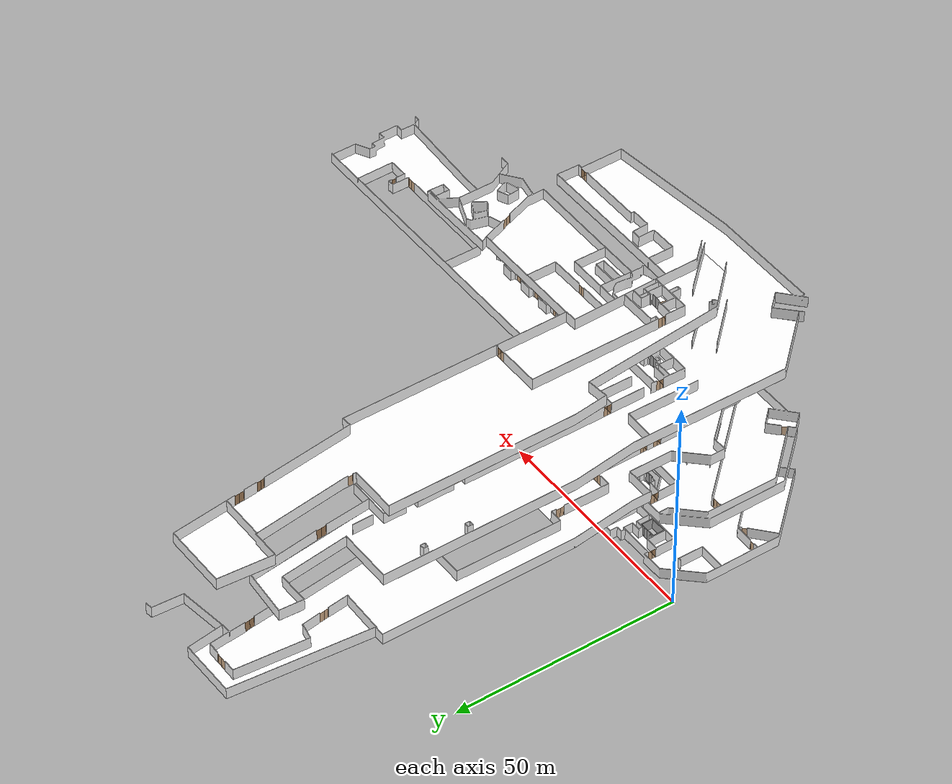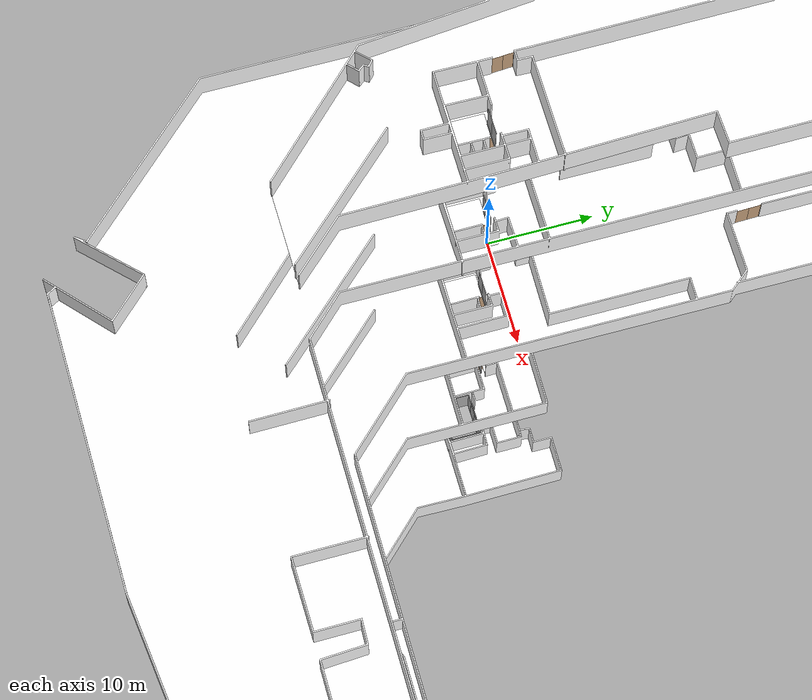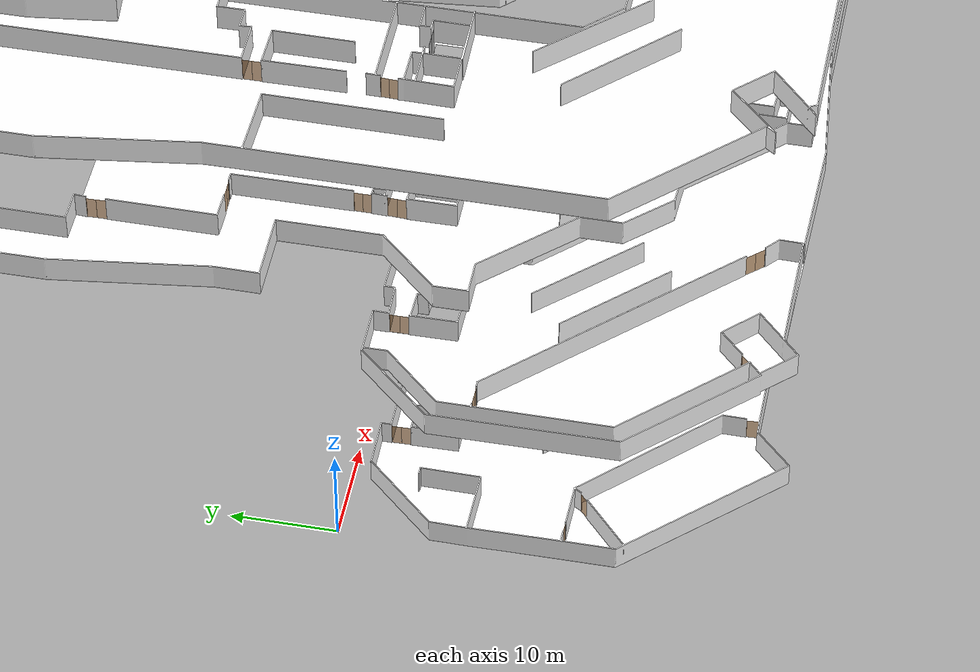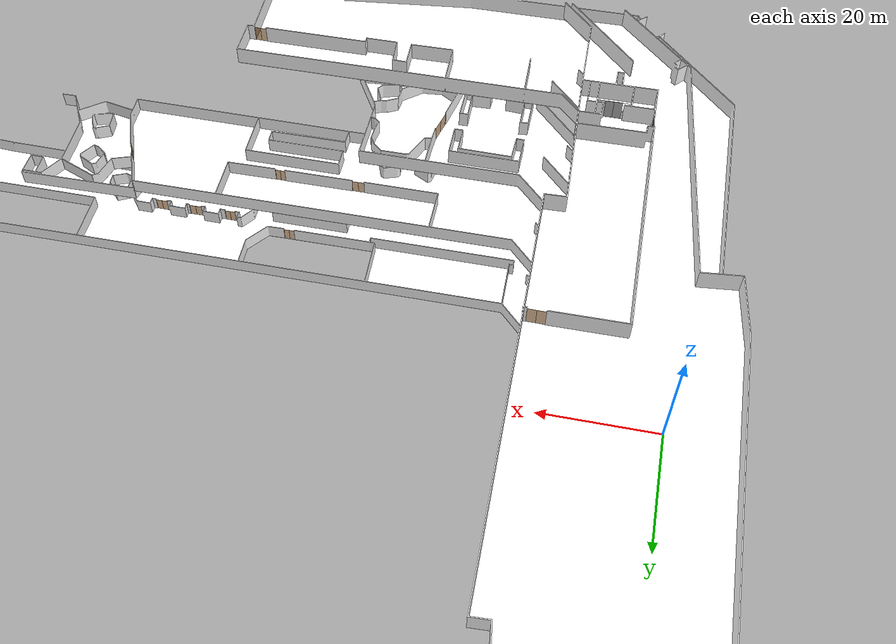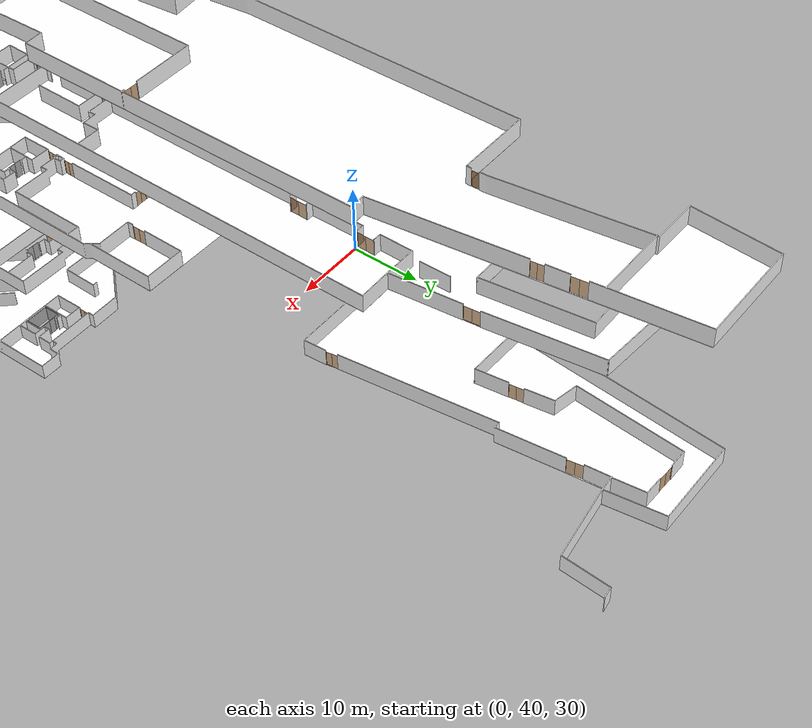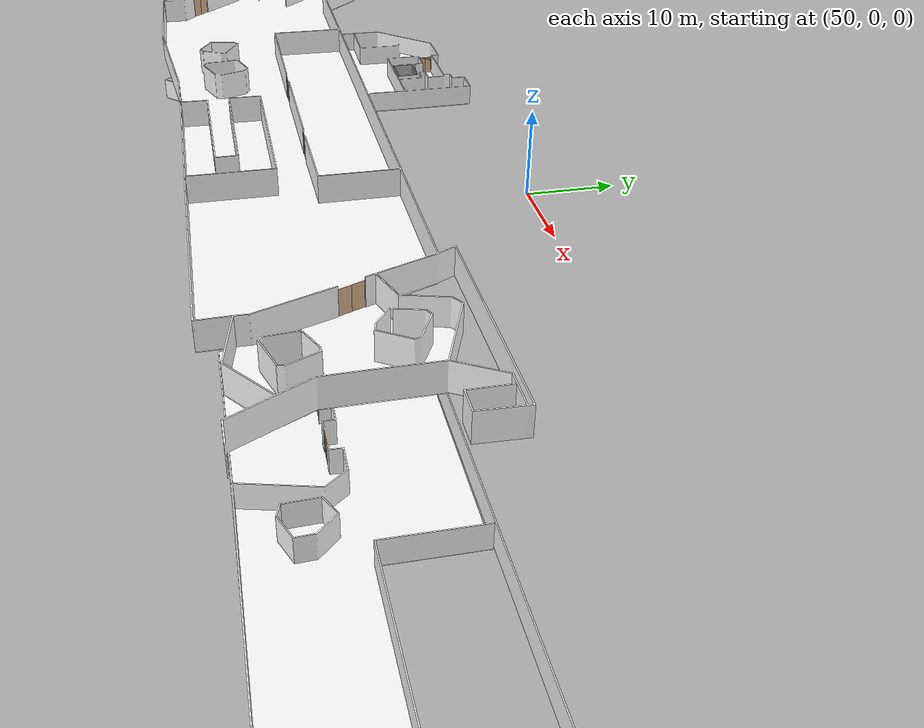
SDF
<sdf version="1.7">
 <world name="world">
  <scene><ambient>0.8 0.8 0.8 1.0</ambient><background>0 0 0</background><grid>false</grid></scene>
  <include><uri>model://sun</uri></include>
  <model name="service-lobby_L2_door">
   <pose>11.583885996739852 -3.5446351422596525 0.0 0 0 1.5909737471841932</pose>
   <link name="right">
    <pose>0.466974485234723 0 1.11 0 0 0</pose>
    <visual name="right_visual">
     <geometry><box><size>0.923948970469446 0.03 2.2</size></box></geometry>
     <material><ambient>0.5 0.25 0 0.6</ambient><diffuse>0.5 0.25 0 0.6</diffuse></material>
    </visual>
    <collision name="right_collision">
     <geometry><box><size>0.923948970469446 0.03 2.2</size></box></geometry>
     <surface><contact><collide_bitmask>0x02</collide_bitmask></contact></surface>
    </collision>
    <inertial>
     <mass>50.0</mass>
     <inertia><ixx>20.17041666666667</ixx><iyy>23.72367375013146</iyy><izz>3.5607570834647886</izz></inertia>
    </inertial>
   </link>
   <joint name="right_joint" type="revolute">
    <parent>world</parent>
    <child>right</child>
    <axis><xyz>0 0 1</xyz><limit><lower>0</lower><upper>1.57</upper></limit></axis>
    <pose>0.466974485234723 0 0 0 0 0</pose>
   </joint>
   <link name="left">
    <pose>-0.466974485234723 0 1.11 0 0 0</pose>
    <visual name="left_visual">
     <geometry><box><size>0.923948970469446 0.03 2.2</size></box></geometry>
     <material><ambient>0.5 0.25 0 0.6</ambient><diffuse>0.5 0.25 0 0.6</diffuse></material>
    </visual>
    <collision name="left_collision">
     <geometry><box><size>0.923948970469446 0.03 2.2</size></box></geometry>
     <surface><contact><collide_bitmask>0x02</collide_bitmask></contact></surface>
    </collision>
    <inertial>
     <mass>50.0</mass>
     <inertia><ixx>20.17041666666667</ixx><iyy>23.72367375013146</iyy><izz>3.5607570834647886</izz></inertia>
    </inertial>
   </link>
   <joint name="left_joint" type="revolute">
    <parent>world</parent>
    <child>left</child>
    <axis><xyz>0 0 1</xyz><limit><lower>-1.57</lower><upper>0</upper></limit></axis>
    <pose>-0.466974485234723 0 0 0 0 0</pose>
   </joint>
   <plugin name="door" filename="libdoor.so">
    <v_max_door>0.5</v_max_door>
    <a_max_door>0.3</a_max_door>
    <a_nom_door>0.15</a_nom_door>
    <dx_min_door>0.01</dx_min_door>
    <f_max_door>500.0</f_max_door>
    <door name="service-lobby_L2_door" type="DoubleSwingDoor" left_joint_name="left_joint" right_joint_name="right_joint"/>
   </plugin>
  </model>
  <model name="store1_L2_door">
   <pose>2.380276734254918 -20.478845790999117 0.0 0 0 3.096348701177637</pose>
   <link name="right">
    <pose>0 0 1.11 0 0 0</pose>
    <visual name="right_visual">
     <geometry><box><size>1.151723939463859 0.03 2.2</size></box></geometry>
     <material><ambient>0.5 0.25 0 0.6</ambient><diffuse>0.5 0.25 0 0.6</diffuse></material>
    </visual>
    <collision name="right_collision">
     <geometry><box><size>1.151723939463859 0.03 2.2</size></box></geometry>
     <surface><contact><collide_bitmask>0x02</collide_bitmask></contact></surface>
    </collision>
    <inertial>
     <mass>50.0</mass>
     <inertia><ixx>20.17041666666667</ixx><iyy>25.693616803058966</iyy><izz>5.530700136392294</izz></inertia>
    </inertial>
   </link>
   <joint name="right_joint" type="revolute">
    <parent>world</parent>
    <child>right</child>
    <axis><xyz>0 0 1</xyz><limit><lower>0</lower><upper>1.57</upper></limit></axis>
    <pose>0.5808619697319295 0 0 0 0 0</pose>
   </joint>
   <plugin name="door" filename="libdoor.so">
    <v_max_door>0.5</v_max_door>
    <a_max_door>0.3</a_max_door>
    <a_nom_door>0.15</a_nom_door>
    <dx_min_door>0.01</dx_min_door>
    <f_max_door>500.0</f_max_door>
    <door name="store1_L2_door" type="SwingDoor" left_joint_name="empty_joint" right_joint_name="right_joint"/>
   </plugin>
  </model>
  <model name="gallery1_L2_door">
   <pose>6.261198334816716 -21.62660015753498 0.0 0 0 -2.409637318313143</pose>
   <link name="right">
    <pose>0 0 1.11 0 0 0</pose>
    <visual name="right_visual">
     <geometry><box><size>1.0571584480211045 0.03 2.2</size></box></geometry>
     <material><ambient>0.5 0.25 0 0.6</ambient><diffuse>0.5 0.25 0 0.6</diffuse></material>
    </visual>
    <collision name="right_collision">
     <geometry><box><size>1.0571584480211045 0.03 2.2</size></box></geometry>
     <surface><contact><collide_bitmask>0x02</collide_bitmask></contact></surface>
    </collision>
    <inertial>
     <mass>50.0</mass>
     <inertia><ixx>20.17041666666667</ixx><iyy>24.823266600926633</iyy><izz>4.660349934259959</izz></inertia>
    </inertial>
   </link>
   <joint name="right_joint" type="revolute">
    <parent>world</parent>
    <child>right</child>
    <axis><xyz>0 0 1</xyz><limit><lower>0</lower><upper>1.57</upper></limit></axis>
    <pose>0.5335792240105522 0 0 0 0 0</pose>
   </joint>
   <plugin name="door" filename="libdoor.so">
    <v_max_door>0.5</v_max_door>
    <a_max_door>0.3</a_max_door>
    <a_nom_door>0.15</a_nom_door>
    <dx_min_door>0.01</dx_min_door>
    <f_max_door>500.0</f_max_door>
    <door name="gallery1_L2_door" type="SwingDoor" left_joint_name="empty_joint" right_joint_name="right_joint"/>
   </plugin>
  </model>
  <model name="gallery2_L2_door">
   <pose>18.40629000949299 -35.29713352360652 0.0 0 0 1.6183057218093173</pose>
   <link name="right">
    <pose>0 0 1.11 0 0 0</pose>
    <visual name="right_visual">
     <geometry><box><size>1.188372499816606 0.03 2.2</size></box></geometry>
     <material><ambient>0.5 0.25 0 0.6</ambient><diffuse>0.5 0.25 0 0.6</diffuse></material>
    </visual>
    <collision name="right_collision">
     <geometry><box><size>1.188372499816606 0.03 2.2</size></box></geometry>
     <surface><contact><collide_bitmask>0x02</collide_bitmask></contact></surface>
    </collision>
    <inertial>
     <mass>50.0</mass>
     <inertia><ixx>20.17041666666667</ixx><iyy>26.050954993001543</iyy><izz>5.888038326334873</izz></inertia>
    </inertial>
   </link>
   <joint name="right_joint" type="revolute">
    <parent>world</parent>
    <child>right</child>
    <axis><xyz>0 0 -1</xyz><limit><lower>0</lower><upper>1.57</upper></limit></axis>
    <pose>0.599186249908303 0 0 0 0 0</pose>
   </joint>
   <plugin name="door" filename="libdoor.so">
    <v_max_door>0.5</v_max_door>
    <a_max_door>0.3</a_max_door>
    <a_nom_door>0.15</a_nom_door>
    <dx_min_door>0.01</dx_min_door>
    <f_max_door>500.0</f_max_door>
    <door name="gallery2_L2_door" type="SwingDoor" left_joint_name="empty_joint" right_joint_name="right_joint"/>
   </plugin>
  </model>
  <model name="smokestop_L2_door">
   <pose>66.48132581454672 -26.345807378045023 0.0 0 0 3.141592653589793</pose>
   <link name="right">
    <pose>0.4753726148826871 0 1.11 0 0 0</pose>
    <visual name="right_visual">
     <geometry><box><size>0.9407452297653742 0.03 2.2</size></box></geometry>
     <material><ambient>0.5 0.25 0 0.6</ambient><diffuse>0.5 0.25 0 0.6</diffuse></material>
    </visual>
    <collision name="right_collision">
     <geometry><box><size>0.9407452297653742 0.03 2.2</size></box></geometry>
     <surface><contact><collide_bitmask>0x02</collide_bitmask></contact></surface>
    </collision>
    <inertial>
     <mass>50.0</mass>
     <inertia><ixx>20.17041666666667</ixx><iyy>23.854173280526282</iyy><izz>3.6912566138596117</izz></inertia>
    </inertial>
   </link>
   <joint name="right_joint" type="revolute">
    <parent>world</parent>
    <child>right</child>
    <axis><xyz>0 0 1</xyz><limit><lower>0</lower><upper>1.57</upper></limit></axis>
    <pose>0.4753726148826871 0 0 0 0 0</pose>
   </joint>
   <link name="left">
    <pose>-0.4753726148826871 0 1.11 0 0 0</pose>
    <visual name="left_visual">
     <geometry><box><size>0.9407452297653742 0.03 2.2</size></box></geometry>
     <material><ambient>0.5 0.25 0 0.6</ambient><diffuse>0.5 0.25 0 0.6</diffuse></material>
    </visual>
    <collision name="left_collision">
     <geometry><box><size>0.9407452297653742 0.03 2.2</size></box></geometry>
     <surface><contact><collide_bitmask>0x02</collide_bitmask></contact></surface>
    </collision>
    <inertial>
     <mass>50.0</mass>
     <inertia><ixx>20.17041666666667</ixx><iyy>23.854173280526282</iyy><izz>3.6912566138596117</izz></inertia>
    </inertial>
   </link>
   <joint name="left_joint" type="revolute">
    <parent>world</parent>
    <child>left</child>
    <axis><xyz>0 0 1</xyz><limit><lower>-1.57</lower><upper>0</upper></limit></axis>
    <pose>-0.4753726148826871 0 0 0 0 0</pose>
   </joint>
   <plugin name="door" filename="libdoor.so">
    <v_max_door>0.5</v_max_door>
    <a_max_door>0.3</a_max_door>
    <a_nom_door>0.15</a_nom_door>
    <dx_min_door>0.01</dx_min_door>
    <f_max_door>500.0</f_max_door>
    <door name="smokestop_L2_door" type="DoubleSwingDoor" left_joint_name="left_joint" right_joint_name="right_joint"/>
   </plugin>
  </model>
  <model name="interest1_L2_door">
   <pose>77.66993731092396 -28.411918169770473 0.0 0 0 3.1267913796408227</pose>
   <link name="right">
    <pose>0.4871143431532625 0 1.11 0 0 0</pose>
    <visual name="right_visual">
     <geometry><box><size>0.964228686306525 0.03 2.2</size></box></geometry>
     <material><ambient>0.5 0.25 0 0.6</ambient><diffuse>0.5 0.25 0 0.6</diffuse></material>
    </visual>
    <collision name="right_collision">
     <geometry><box><size>0.964228686306525 0.03 2.2</size></box></geometry>
     <surface><contact><collide_bitmask>0x02</collide_bitmask></contact></surface>
    </collision>
    <inertial>
     <mass>50.0</mass>
     <inertia><ixx>20.17041666666667</ixx><iyy>24.040570664568367</iyy><izz>3.877653997901696</izz></inertia>
    </inertial>
   </link>
   <joint name="right_joint" type="revolute">
    <parent>world</parent>
    <child>right</child>
    <axis><xyz>0 0 1</xyz><limit><lower>0</lower><upper>1.57</upper></limit></axis>
    <pose>0.4871143431532625 0 0 0 0 0</pose>
   </joint>
   <link name="left">
    <pose>-0.4871143431532625 0 1.11 0 0 0</pose>
    <visual name="left_visual">
     <geometry><box><size>0.964228686306525 0.03 2.2</size></box></geometry>
     <material><ambient>0.5 0.25 0 0.6</ambient><diffuse>0.5 0.25 0 0.6</diffuse></material>
    </visual>
    <collision name="left_collision">
     <geometry><box><size>0.964228686306525 0.03 2.2</size></box></geometry>
     <surface><contact><collide_bitmask>0x02</collide_bitmask></contact></surface>
    </collision>
    <inertial>
     <mass>50.0</mass>
     <inertia><ixx>20.17041666666667</ixx><iyy>24.040570664568367</iyy><izz>3.877653997901696</izz></inertia>
    </inertial>
   </link>
   <joint name="left_joint" type="revolute">
    <parent>world</parent>
    <child>left</child>
    <axis><xyz>0 0 1</xyz><limit><lower>-1.57</lower><upper>0</upper></limit></axis>
    <pose>-0.4871143431532625 0 0 0 0 0</pose>
   </joint>
   <plugin name="door" filename="libdoor.so">
    <v_max_door>0.5</v_max_door>
    <a_max_door>0.3</a_max_door>
    <a_nom_door>0.15</a_nom_door>
    <dx_min_door>0.01</dx_min_door>
    <f_max_door>500.0</f_max_door>
    <door name="interest1_L2_door" type="DoubleSwingDoor" left_joint_name="left_joint" right_joint_name="right_joint"/>
   </plugin>
  </model>
  <model name="interest2_L2_door">
   <pose>83.95019752229541 -28.415195283218274 0.0 0 0 -3.1317800867285626</pose>
   <link name="right">
    <pose>0.5677599291332157 0 1.11 0 0 0</pose>
    <visual name="right_visual">
     <geometry><box><size>1.1255198582664314 0.03 2.2</size></box></geometry>
     <material><ambient>0.5 0.25 0 0.6</ambient><diffuse>0.5 0.25 0 0.6</diffuse></material>
    </visual>
    <collision name="right_collision">
     <geometry><box><size>1.1255198582664314 0.03 2.2</size></box></geometry>
     <surface><contact><collide_bitmask>0x02</collide_bitmask></contact></surface>
    </collision>
    <inertial>
     <mass>50.0</mass>
     <inertia><ixx>20.17041666666667</ixx><iyy>25.44497896396704</iyy><izz>5.282062297300366</izz></inertia>
    </inertial>
   </link>
   <joint name="right_joint" type="revolute">
    <parent>world</parent>
    <child>right</child>
    <axis><xyz>0 0 1</xyz><limit><lower>0</lower><upper>1.57</upper></limit></axis>
    <pose>0.5677599291332157 0 0 0 0 0</pose>
   </joint>
   <link name="left">
    <pose>-0.5677599291332157 0 1.11 0 0 0</pose>
    <visual name="left_visual">
     <geometry><box><size>1.1255198582664314 0.03 2.2</size></box></geometry>
     <material><ambient>0.5 0.25 0 0.6</ambient><diffuse>0.5 0.25 0 0.6</diffuse></material>
    </visual>
    <collision name="left_collision">
     <geometry><box><size>1.1255198582664314 0.03 2.2</size></box></geometry>
     <surface><contact><collide_bitmask>0x02</collide_bitmask></contact></surface>
    </collision>
    <inertial>
     <mass>50.0</mass>
     <inertia><ixx>20.17041666666667</ixx><iyy>25.44497896396704</iyy><izz>5.282062297300366</izz></inertia>
    </inertial>
   </link>
   <joint name="left_joint" type="revolute">
    <parent>world</parent>
    <child>left</child>
    <axis><xyz>0 0 1</xyz><limit><lower>-1.57</lower><upper>0</upper></limit></axis>
    <pose>-0.5677599291332157 0 0 0 0 0</pose>
   </joint>
   <plugin name="door" filename="libdoor.so">
    <v_max_door>0.5</v_max_door>
    <a_max_door>0.3</a_max_door>
    <a_nom_door>0.15</a_nom_door>
    <dx_min_door>0.01</dx_min_door>
    <f_max_door>500.0</f_max_door>
    <door name="interest2_L2_door" type="DoubleSwingDoor" left_joint_name="left_joint" right_joint_name="right_joint"/>
   </plugin>
  </model>
  <model name="interest3_L2_door">
   <pose>90.14361422730005 -28.463805799360703 0.0 0 0 3.141592653589793</pose>
   <link name="right">
    <pose>0.5296634610013093 0 1.11 0 0 0</pose>
    <visual name="right_visual">
     <geometry><box><size>1.0493269220026187 0.03 2.2</size></box></geometry>
     <material><ambient>0.5 0.25 0 0.6</ambient><diffuse>0.5 0.25 0 0.6</diffuse></material>
    </visual>
    <collision name="right_collision">
     <geometry><box><size>1.0493269220026187 0.03 2.2</size></box></geometry>
     <surface><contact><collide_bitmask>0x02</collide_bitmask></contact></surface>
    </collision>
    <inertial>
     <mass>50.0</mass>
     <inertia><ixx>20.17041666666667</ixx><iyy>24.75452912183121</iyy><izz>4.591612455164541</izz></inertia>
    </inertial>
   </link>
   <joint name="right_joint" type="revolute">
    <parent>world</parent>
    <child>right</child>
    <axis><xyz>0 0 1</xyz><limit><lower>0</lower><upper>1.57</upper></limit></axis>
    <pose>0.5296634610013093 0 0 0 0 0</pose>
   </joint>
   <link name="left">
    <pose>-0.5296634610013093 0 1.11 0 0 0</pose>
    <visual name="left_visual">
     <geometry><box><size>1.0493269220026187 0.03 2.2</size></box></geometry>
     <material><ambient>0.5 0.25 0 0.6</ambient><diffuse>0.5 0.25 0 0.6</diffuse></material>
    </visual>
    <collision name="left_collision">
     <geometry><box><size>1.0493269220026187 0.03 2.2</size></box></geometry>
     <surface><contact><collide_bitmask>0x02</collide_bitmask></contact></surface>
    </collision>
    <inertial>
     <mass>50.0</mass>
     <inertia><ixx>20.17041666666667</ixx><iyy>24.75452912183121</iyy><izz>4.591612455164541</izz></inertia>
    </inertial>
   </link>
   <joint name="left_joint" type="revolute">
    <parent>world</parent>
    <child>left</child>
    <axis><xyz>0 0 1</xyz><limit><lower>-1.57</lower><upper>0</upper></limit></axis>
    <pose>-0.5296634610013093 0 0 0 0 0</pose>
   </joint>
   <plugin name="door" filename="libdoor.so">
    <v_max_door>0.5</v_max_door>
    <a_max_door>0.3</a_max_door>
    <a_nom_door>0.15</a_nom_door>
    <dx_min_door>0.01</dx_min_door>
    <f_max_door>500.0</f_max_door>
    <door name="interest3_L2_door" type="DoubleSwingDoor" left_joint_name="left_joint" right_joint_name="right_joint"/>
   </plugin>
  </model>
  <model name="firefighting_L2_door">
   <pose>126.6312138293788 -26.76899196127144 0.0 0 0 3.1135261265353575</pose>
   <link name="right">
    <pose>0.5663717167232082 0 1.11 0 0 0</pose>
    <visual name="right_visual">
     <geometry><box><size>1.1227434334464164 0.03 2.2</size></box></geometry>
     <material><ambient>0.5 0.25 0 0.6</ambient><diffuse>0.5 0.25 0 0.6</diffuse></material>
    </visual>
    <collision name="right_collision">
     <geometry><box><size>1.1227434334464164 0.03 2.2</size></box></geometry>
     <surface><contact><collide_bitmask>0x02</collide_bitmask></contact></surface>
    </collision>
    <inertial>
     <mass>50.0</mass>
     <inertia><ixx>20.17041666666667</ixx><iyy>25.418970072279368</iyy><izz>5.256053405612698</izz></inertia>
    </inertial>
   </link>
   <joint name="right_joint" type="revolute">
    <parent>world</parent>
    <child>right</child>
    <axis><xyz>0 0 1</xyz><limit><lower>0</lower><upper>1.57</upper></limit></axis>
    <pose>0.5663717167232082 0 0 0 0 0</pose>
   </joint>
   <link name="left">
    <pose>-0.5663717167232082 0 1.11 0 0 0</pose>
    <visual name="left_visual">
     <geometry><box><size>1.1227434334464164 0.03 2.2</size></box></geometry>
     <material><ambient>0.5 0.25 0 0.6</ambient><diffuse>0.5 0.25 0 0.6</diffuse></material>
    </visual>
    <collision name="left_collision">
     <geometry><box><size>1.1227434334464164 0.03 2.2</size></box></geometry>
     <surface><contact><collide_bitmask>0x02</collide_bitmask></contact></surface>
    </collision>
    <inertial>
     <mass>50.0</mass>
     <inertia><ixx>20.17041666666667</ixx><iyy>25.418970072279368</iyy><izz>5.256053405612698</izz></inertia>
    </inertial>
   </link>
   <joint name="left_joint" type="revolute">
    <parent>world</parent>
    <child>left</child>
    <axis><xyz>0 0 1</xyz><limit><lower>-1.57</lower><upper>0</upper></limit></axis>
    <pose>-0.5663717167232082 0 0 0 0 0</pose>
   </joint>
   <plugin name="door" filename="libdoor.so">
    <v_max_door>0.5</v_max_door>
    <a_max_door>0.3</a_max_door>
    <a_nom_door>0.15</a_nom_door>
    <dx_min_door>0.01</dx_min_door>
    <f_max_door>500.0</f_max_door>
    <door name="firefighting_L2_door" type="DoubleSwingDoor" left_joint_name="left_joint" right_joint_name="right_joint"/>
   </plugin>
  </model>
  <model name="store2_L2_door">
   <pose>129.1604353698364 -24.038774129348525 0.0 0 0 1.5707963267948966</pose>
   <link name="right">
    <pose>0 0 1.11 0 0 0</pose>
    <visual name="right_visual">
     <geometry><box><size>1.1117559331832838 0.03 2.2</size></box></geometry>
     <material><ambient>0.5 0.25 0 0.6</ambient><diffuse>0.5 0.25 0 0.6</diffuse></material>
    </visual>
    <collision name="right_collision">
     <geometry><box><size>1.1117559331832838 0.03 2.2</size></box></geometry>
     <surface><contact><collide_bitmask>0x02</collide_bitmask></contact></surface>
    </collision>
    <inertial>
     <mass>50.0</mass>
     <inertia><ixx>20.17041666666667</ixx><iyy>25.31667189570098</iyy><izz>5.153755229034309</izz></inertia>
    </inertial>
   </link>
   <joint name="right_joint" type="revolute">
    <parent>world</parent>
    <child>right</child>
    <axis><xyz>0 0 1</xyz><limit><lower>0</lower><upper>1.57</upper></limit></axis>
    <pose>0.5608779665916419 0 0 0 0 0</pose>
   </joint>
   <plugin name="door" filename="libdoor.so">
    <v_max_door>0.5</v_max_door>
    <a_max_door>0.3</a_max_door>
    <a_nom_door>0.15</a_nom_door>
    <dx_min_door>0.01</dx_min_door>
    <f_max_door>500.0</f_max_door>
    <door name="store2_L2_door" type="SwingDoor" left_joint_name="empty_joint" right_joint_name="right_joint"/>
   </plugin>
  </model>
  <include><name>trl_TRL_L2</name><uri>model://trl_TRL_L2</uri></include>
  <model name="service-lobby_L3_door">
   <pose>11.595813681360958 -3.6346702538411506 15.0 0 0 1.5814037695309886</pose>
   <link name="right">
    <pose>0.4923775692285238 0 1.11 0 0 0</pose>
    <visual name="right_visual">
     <geometry><box><size>0.9747551384570476 0.03 2.2</size></box></geometry>
     <material><ambient>0.5 0.25 0 0.6</ambient><diffuse>0.5 0.25 0 0.6</diffuse></material>
    </visual>
    <collision name="right_collision">
     <geometry><box><size>0.9747551384570476 0.03 2.2</size></box></geometry>
     <surface><contact><collide_bitmask>0x02</collide_bitmask></contact></surface>
    </collision>
    <inertial>
     <mass>50.0</mass>
     <inertia><ixx>20.17041666666667</ixx><iyy>24.12561491645175</iyy><izz>3.962698249785076</izz></inertia>
    </inertial>
   </link>
   <joint name="right_joint" type="revolute">
    <parent>world</parent>
    <child>right</child>
    <axis><xyz>0 0 1</xyz><limit><lower>0</lower><upper>1.57</upper></limit></axis>
    <pose>0.4923775692285238 0 0 0 0 0</pose>
   </joint>
   <link name="left">
    <pose>-0.4923775692285238 0 1.11 0 0 0</pose>
    <visual name="left_visual">
     <geometry><box><size>0.9747551384570476 0.03 2.2</size></box></geometry>
     <material><ambient>0.5 0.25 0 0.6</ambient><diffuse>0.5 0.25 0 0.6</diffuse></material>
    </visual>
    <collision name="left_collision">
     <geometry><box><size>0.9747551384570476 0.03 2.2</size></box></geometry>
     <surface><contact><collide_bitmask>0x02</collide_bitmask></contact></surface>
    </collision>
    <inertial>
     <mass>50.0</mass>
     <inertia><ixx>20.17041666666667</ixx><iyy>24.12561491645175</iyy><izz>3.962698249785076</izz></inertia>
    </inertial>
   </link>
   <joint name="left_joint" type="revolute">
    <parent>world</parent>
    <child>left</child>
    <axis><xyz>0 0 1</xyz><limit><lower>-1.57</lower><upper>0</upper></limit></axis>
    <pose>-0.4923775692285238 0 0 0 0 0</pose>
   </joint>
   <plugin name="door" filename="libdoor.so">
    <v_max_door>0.5</v_max_door>
    <a_max_door>0.3</a_max_door>
    <a_nom_door>0.15</a_nom_door>
    <dx_min_door>0.01</dx_min_door>
    <f_max_door>500.0</f_max_door>
    <door name="service-lobby_L3_door" type="DoubleSwingDoor" left_joint_name="left_joint" right_joint_name="right_joint"/>
   </plugin>
  </model>
  <model name="playground1_L3_door">
   <pose>3.322548309158081 -12.04451082373328 15.0 0 0 3.1310501428320436</pose>
   <link name="right">
    <pose>0.5202364664339312 0 1.11 0 0 0</pose>
    <visual name="right_visual">
     <geometry><box><size>1.0304729328678623 0.03 2.2</size></box></geometry>
     <material><ambient>0.5 0.25 0 0.6</ambient><diffuse>0.5 0.25 0 0.6</diffuse></material>
    </visual>
    <collision name="right_collision">
     <geometry><box><size>1.0304729328678623 0.03 2.2</size></box></geometry>
     <surface><contact><collide_bitmask>0x02</collide_bitmask></contact></surface>
    </collision>
    <inertial>
     <mass>50.0</mass>
     <inertia><ixx>20.17041666666667</ixx><iyy>24.591143605722063</iyy><izz>4.428226939055391</izz></inertia>
    </inertial>
   </link>
   <joint name="right_joint" type="revolute">
    <parent>world</parent>
    <child>right</child>
    <axis><xyz>0 0 1</xyz><limit><lower>0</lower><upper>1.57</upper></limit></axis>
    <pose>0.5202364664339312 0 0 0 0 0</pose>
   </joint>
   <link name="left">
    <pose>-0.5202364664339312 0 1.11 0 0 0</pose>
    <visual name="left_visual">
     <geometry><box><size>1.0304729328678623 0.03 2.2</size></box></geometry>
     <material><ambient>0.5 0.25 0 0.6</ambient><diffuse>0.5 0.25 0 0.6</diffuse></material>
    </visual>
    <collision name="left_collision">
     <geometry><box><size>1.0304729328678623 0.03 2.2</size></box></geometry>
     <surface><contact><collide_bitmask>0x02</collide_bitmask></contact></surface>
    </collision>
    <inertial>
     <mass>50.0</mass>
     <inertia><ixx>20.17041666666667</ixx><iyy>24.591143605722063</iyy><izz>4.428226939055391</izz></inertia>
    </inertial>
   </link>
   <joint name="left_joint" type="revolute">
    <parent>world</parent>
    <child>left</child>
    <axis><xyz>0 0 1</xyz><limit><lower>-1.57</lower><upper>0</upper></limit></axis>
    <pose>-0.5202364664339312 0 0 0 0 0</pose>
   </joint>
   <plugin name="door" filename="libdoor.so">
    <v_max_door>0.5</v_max_door>
    <a_max_door>0.3</a_max_door>
    <a_nom_door>0.15</a_nom_door>
    <dx_min_door>0.01</dx_min_door>
    <f_max_door>500.0</f_max_door>
    <door name="playground1_L3_door" type="DoubleSwingDoor" left_joint_name="left_joint" right_joint_name="right_joint"/>
   </plugin>
  </model>
  <model name="playground2_L3_door">
   <pose>25.269429861230506 -33.89215628092748 15.0 0 0 2.2918884869734164</pose>
   <link name="right">
    <pose>0.5427981633840488 0 1.11 0 0 0</pose>
    <visual name="right_visual">
     <geometry><box><size>1.0755963267680977 0.03 2.2</size></box></geometry>
     <material><ambient>0.5 0.25 0 0.6</ambient><diffuse>0.5 0.25 0 0.6</diffuse></material>
    </visual>
    <collision name="right_collision">
     <geometry><box><size>1.0755963267680977 0.03 2.2</size></box></geometry>
     <surface><contact><collide_bitmask>0x02</collide_bitmask></contact></surface>
    </collision>
    <inertial>
     <mass>50.0</mass>
     <inertia><ixx>20.17041666666667</ixx><iyy>24.98711440898761</iyy><izz>4.824197742320935</izz></inertia>
    </inertial>
   </link>
   <joint name="right_joint" type="revolute">
    <parent>world</parent>
    <child>right</child>
    <axis><xyz>0 0 1</xyz><limit><lower>0</lower><upper>1.57</upper></limit></axis>
    <pose>0.5427981633840488 0 0 0 0 0</pose>
   </joint>
   <link name="left">
    <pose>-0.5427981633840488 0 1.11 0 0 0</pose>
    <visual name="left_visual">
     <geometry><box><size>1.0755963267680977 0.03 2.2</size></box></geometry>
     <material><ambient>0.5 0.25 0 0.6</ambient><diffuse>0.5 0.25 0 0.6</diffuse></material>
    </visual>
    <collision name="left_collision">
     <geometry><box><size>1.0755963267680977 0.03 2.2</size></box></geometry>
     <surface><contact><collide_bitmask>0x02</collide_bitmask></contact></surface>
    </collision>
    <inertial>
     <mass>50.0</mass>
     <inertia><ixx>20.17041666666667</ixx><iyy>24.98711440898761</iyy><izz>4.824197742320935</izz></inertia>
    </inertial>
   </link>
   <joint name="left_joint" type="revolute">
    <parent>world</parent>
    <child>left</child>
    <axis><xyz>0 0 1</xyz><limit><lower>-1.57</lower><upper>0</upper></limit></axis>
    <pose>-0.5427981633840488 0 0 0 0 0</pose>
   </joint>
   <plugin name="door" filename="libdoor.so">
    <v_max_door>0.5</v_max_door>
    <a_max_door>0.3</a_max_door>
    <a_nom_door>0.15</a_nom_door>
    <dx_min_door>0.01</dx_min_door>
    <f_max_door>500.0</f_max_door>
    <door name="playground2_L3_door" type="DoubleSwingDoor" left_joint_name="left_joint" right_joint_name="right_joint"/>
   </plugin>
  </model>
  <model name="store1_L3_door">
   <pose>12.176113249509854 -34.98149825992466 15.0 0 0 -2.2922465724971652</pose>
   <link name="right">
    <pose>0 0 1.11 0 0 0</pose>
    <visual name="right_visual">
     <geometry><box><size>1.218709339195872 0.03 2.2</size></box></geometry>
     <material><ambient>0.5 0.25 0 0.6</ambient><diffuse>0.5 0.25 0 0.6</diffuse></material>
    </visual>
    <collision name="right_collision">
     <geometry><box><size>1.218709339195872 0.03 2.2</size></box></geometry>
     <surface><contact><collide_bitmask>0x02</collide_bitmask></contact></surface>
    </collision>
    <inertial>
     <mass>50.0</mass>
     <inertia><ixx>20.17041666666667</ixx><iyy>26.3552185560135</iyy><izz>6.19230188934683</izz></inertia>
    </inertial>
   </link>
   <joint name="right_joint" type="revolute">
    <parent>world</parent>
    <child>right</child>
    <axis><xyz>0 0 -1</xyz><limit><lower>0</lower><upper>1.57</upper></limit></axis>
    <pose>0.614354669597936 0 0 0 0 0</pose>
   </joint>
   <plugin name="door" filename="libdoor.so">
    <v_max_door>0.5</v_max_door>
    <a_max_door>0.3</a_max_door>
    <a_nom_door>0.15</a_nom_door>
    <dx_min_door>0.01</dx_min_door>
    <f_max_door>500.0</f_max_door>
    <door name="store1_L3_door" type="SwingDoor" left_joint_name="empty_joint" right_joint_name="right_joint"/>
   </plugin>
  </model>
  <model name="corridor_L3_door">
   <pose>53.71945501726545 -26.568957076509808 15.0 0 0 -3.133450067548624</pose>
   <link name="right">
    <pose>0.5173317745371737 0 1.11 0 0 0</pose>
    <visual name="right_visual">
     <geometry><box><size>1.0246635490743474 0.03 2.2</size></box></geometry>
     <material><ambient>0.5 0.25 0 0.6</ambient><diffuse>0.5 0.25 0 0.6</diffuse></material>
    </visual>
    <collision name="right_collision">
     <geometry><box><size>1.0246635490743474 0.03 2.2</size></box></geometry>
     <surface><contact><collide_bitmask>0x02</collide_bitmask></contact></surface>
    </collision>
    <inertial>
     <mass>50.0</mass>
     <inertia><ixx>20.17041666666667</ixx><iyy>24.54139745334016</iyy><izz>4.37848078667349</izz></inertia>
    </inertial>
   </link>
   <joint name="right_joint" type="revolute">
    <parent>world</parent>
    <child>right</child>
    <axis><xyz>0 0 1</xyz><limit><lower>0</lower><upper>1.57</upper></limit></axis>
    <pose>0.5173317745371737 0 0 0 0 0</pose>
   </joint>
   <link name="left">
    <pose>-0.5173317745371737 0 1.11 0 0 0</pose>
    <visual name="left_visual">
     <geometry><box><size>1.0246635490743474 0.03 2.2</size></box></geometry>
     <material><ambient>0.5 0.25 0 0.6</ambient><diffuse>0.5 0.25 0 0.6</diffuse></material>
    </visual>
    <collision name="left_collision">
     <geometry><box><size>1.0246635490743474 0.03 2.2</size></box></geometry>
     <surface><contact><collide_bitmask>0x02</collide_bitmask></contact></surface>
    </collision>
    <inertial>
     <mass>50.0</mass>
     <inertia><ixx>20.17041666666667</ixx><iyy>24.54139745334016</iyy><izz>4.37848078667349</izz></inertia>
    </inertial>
   </link>
   <joint name="left_joint" type="revolute">
    <parent>world</parent>
    <child>left</child>
    <axis><xyz>0 0 1</xyz><limit><lower>-1.57</lower><upper>0</upper></limit></axis>
    <pose>-0.5173317745371737 0 0 0 0 0</pose>
   </joint>
   <plugin name="door" filename="libdoor.so">
    <v_max_door>0.5</v_max_door>
    <a_max_door>0.3</a_max_door>
    <a_nom_door>0.15</a_nom_door>
    <dx_min_door>0.01</dx_min_door>
    <f_max_door>500.0</f_max_door>
    <door name="corridor_L3_door" type="DoubleSwingDoor" left_joint_name="left_joint" right_joint_name="right_joint"/>
   </plugin>
  </model>
  <model name="smokestop_L3_door">
   <pose>66.6997172517861 -26.544838673881298 15.0 0 0 3.1292897796821117</pose>
   <link name="right">
    <pose>0.4262980263060661 0 1.11 0 0 0</pose>
    <visual name="right_visual">
     <geometry><box><size>0.8425960526121322 0.03 2.2</size></box></geometry>
     <material><ambient>0.5 0.25 0 0.6</ambient><diffuse>0.5 0.25 0 0.6</diffuse></material>
    </visual>
    <collision name="right_collision">
     <geometry><box><size>0.8425960526121322 0.03 2.2</size></box></geometry>
     <surface><contact><collide_bitmask>0x02</collide_bitmask></contact></surface>
    </collision>
    <inertial>
     <mass>50.0</mass>
     <inertia><ixx>20.17041666666667</ixx><iyy>23.12486711615645</iyy><izz>2.9619504494897795</izz></inertia>
    </inertial>
   </link>
   <joint name="right_joint" type="revolute">
    <parent>world</parent>
    <child>right</child>
    <axis><xyz>0 0 1</xyz><limit><lower>0</lower><upper>1.57</upper></limit></axis>
    <pose>0.4262980263060661 0 0 0 0 0</pose>
   </joint>
   <link name="left">
    <pose>-0.4262980263060661 0 1.11 0 0 0</pose>
    <visual name="left_visual">
     <geometry><box><size>0.8425960526121322 0.03 2.2</size></box></geometry>
     <material><ambient>0.5 0.25 0 0.6</ambient><diffuse>0.5 0.25 0 0.6</diffuse></material>
    </visual>
    <collision name="left_collision">
     <geometry><box><size>0.8425960526121322 0.03 2.2</size></box></geometry>
     <surface><contact><collide_bitmask>0x02</collide_bitmask></contact></surface>
    </collision>
    <inertial>
     <mass>50.0</mass>
     <inertia><ixx>20.17041666666667</ixx><iyy>23.12486711615645</iyy><izz>2.9619504494897795</izz></inertia>
    </inertial>
   </link>
   <joint name="left_joint" type="revolute">
    <parent>world</parent>
    <child>left</child>
    <axis><xyz>0 0 1</xyz><limit><lower>-1.57</lower><upper>0</upper></limit></axis>
    <pose>-0.4262980263060661 0 0 0 0 0</pose>
   </joint>
   <plugin name="door" filename="libdoor.so">
    <v_max_door>0.5</v_max_door>
    <a_max_door>0.3</a_max_door>
    <a_nom_door>0.15</a_nom_door>
    <dx_min_door>0.01</dx_min_door>
    <f_max_door>500.0</f_max_door>
    <door name="smokestop_L3_door" type="DoubleSwingDoor" left_joint_name="left_joint" right_joint_name="right_joint"/>
   </plugin>
  </model>
  <model name="sky_L3_door">
   <pose>92.00251722887253 -26.343846688626595 15.0 0 0 1.9520743057615924</pose>
   <link name="right">
    <pose>0.5803212927918754 0 1.11 0 0 0</pose>
    <visual name="right_visual">
     <geometry><box><size>1.1506425855837508 0.03 2.2</size></box></geometry>
     <material><ambient>0.5 0.25 0 0.6</ambient><diffuse>0.5 0.25 0 0.6</diffuse></material>
    </visual>
    <collision name="right_collision">
     <geometry><box><size>1.1506425855837508 0.03 2.2</size></box></geometry>
     <surface><contact><collide_bitmask>0x02</collide_bitmask></contact></surface>
    </collision>
    <inertial>
     <mass>50.0</mass>
     <inertia><ixx>20.17041666666667</ixx><iyy>25.68324316566192</iyy><izz>5.520326498995247</izz></inertia>
    </inertial>
   </link>
   <joint name="right_joint" type="revolute">
    <parent>world</parent>
    <child>right</child>
    <axis><xyz>0 0 1</xyz><limit><lower>0</lower><upper>1.57</upper></limit></axis>
    <pose>0.5803212927918754 0 0 0 0 0</pose>
   </joint>
   <link name="left">
    <pose>-0.5803212927918754 0 1.11 0 0 0</pose>
    <visual name="left_visual">
     <geometry><box><size>1.1506425855837508 0.03 2.2</size></box></geometry>
     <material><ambient>0.5 0.25 0 0.6</ambient><diffuse>0.5 0.25 0 0.6</diffuse></material>
    </visual>
    <collision name="left_collision">
     <geometry><box><size>1.1506425855837508 0.03 2.2</size></box></geometry>
     <surface><contact><collide_bitmask>0x02</collide_bitmask></contact></surface>
    </collision>
    <inertial>
     <mass>50.0</mass>
     <inertia><ixx>20.17041666666667</ixx><iyy>25.68324316566192</iyy><izz>5.520326498995247</izz></inertia>
    </inertial>
   </link>
   <joint name="left_joint" type="revolute">
    <parent>world</parent>
    <child>left</child>
    <axis><xyz>0 0 1</xyz><limit><lower>-1.57</lower><upper>0</upper></limit></axis>
    <pose>-0.5803212927918754 0 0 0 0 0</pose>
   </joint>
   <plugin name="door" filename="libdoor.so">
    <v_max_door>0.5</v_max_door>
    <a_max_door>0.3</a_max_door>
    <a_nom_door>0.15</a_nom_door>
    <dx_min_door>0.01</dx_min_door>
    <f_max_door>500.0</f_max_door>
    <door name="sky_L3_door" type="DoubleSwingDoor" left_joint_name="left_joint" right_joint_name="right_joint"/>
   </plugin>
  </model>
  <include><name>trl_TRL_L3</name><uri>model://trl_TRL_L3</uri><pose>0 0 15.0 0 0 0</pose></include>
  <model name="outdoor_L4_door">
   <pose>10.295966701163223 93.44173359887864 30.0 0 0 3.1186204261640538</pose>
   <link name="right">
    <pose>0.6397635326972566 0 1.11 0 0 0</pose>
    <visual name="right_visual">
     <geometry><box><size>1.2695270653945132 0.03 2.2</size></box></geometry>
     <material><ambient>0.5 0.25 0 0.6</ambient><diffuse>0.5 0.25 0 0.6</diffuse></material>
    </visual>
    <collision name="right_collision">
     <geometry><box><size>1.2695270653945132 0.03 2.2</size></box></geometry>
     <surface><contact><collide_bitmask>0x02</collide_bitmask></contact></surface>
    </collision>
    <inertial>
     <mass>50.0</mass>
     <inertia><ixx>20.17041666666667</ixx><iyy>26.882079040705026</iyy><izz>6.719162374038352</izz></inertia>
    </inertial>
   </link>
   <joint name="right_joint" type="revolute">
    <parent>world</parent>
    <child>right</child>
    <axis><xyz>0 0 -1</xyz><limit><lower>0</lower><upper>1.57</upper></limit></axis>
    <pose>0.6397635326972566 0 0 0 0 0</pose>
   </joint>
   <link name="left">
    <pose>-0.6397635326972566 0 1.11 0 0 0</pose>
    <visual name="left_visual">
     <geometry><box><size>1.2695270653945132 0.03 2.2</size></box></geometry>
     <material><ambient>0.5 0.25 0 0.6</ambient><diffuse>0.5 0.25 0 0.6</diffuse></material>
    </visual>
    <collision name="left_collision">
     <geometry><box><size>1.2695270653945132 0.03 2.2</size></box></geometry>
     <surface><contact><collide_bitmask>0x02</collide_bitmask></contact></surface>
    </collision>
    <inertial>
     <mass>50.0</mass>
     <inertia><ixx>20.17041666666667</ixx><iyy>26.882079040705026</iyy><izz>6.719162374038352</izz></inertia>
    </inertial>
   </link>
   <joint name="left_joint" type="revolute">
    <parent>world</parent>
    <child>left</child>
    <axis><xyz>0 0 -1</xyz><limit><lower>-1.57</lower><upper>0</upper></limit></axis>
    <pose>-0.6397635326972566 0 0 0 0 0</pose>
   </joint>
   <plugin name="door" filename="libdoor.so">
    <v_max_door>0.5</v_max_door>
    <a_max_door>0.3</a_max_door>
    <a_nom_door>0.15</a_nom_door>
    <dx_min_door>0.01</dx_min_door>
    <f_max_door>500.0</f_max_door>
    <door name="outdoor_L4_door" type="DoubleSwingDoor" left_joint_name="left_joint" right_joint_name="right_joint"/>
   </plugin>
  </model>
  <model name="smokestop_L4_door">
   <pose>15.177878838571637 84.31903757520827 30.0 0 0 1.7378695474989483</pose>
   <link name="right">
    <pose>0.5722634414028462 0 1.11 0 0 0</pose>
    <visual name="right_visual">
     <geometry><box><size>1.1345268828056925 0.03 2.2</size></box></geometry>
     <material><ambient>0.5 0.25 0 0.6</ambient><diffuse>0.5 0.25 0 0.6</diffuse></material>
    </visual>
    <collision name="right_collision">
     <geometry><box><size>1.1345268828056925 0.03 2.2</size></box></geometry>
     <surface><contact><collide_bitmask>0x02</collide_bitmask></contact></surface>
    </collision>
    <inertial>
     <mass>50.0</mass>
     <inertia><ixx>20.17041666666667</ixx><iyy>25.52979686587001</iyy><izz>5.366880199203339</izz></inertia>
    </inertial>
   </link>
   <joint name="right_joint" type="revolute">
    <parent>world</parent>
    <child>right</child>
    <axis><xyz>0 0 1</xyz><limit><lower>0</lower><upper>1.57</upper></limit></axis>
    <pose>0.5722634414028462 0 0 0 0 0</pose>
   </joint>
   <link name="left">
    <pose>-0.5722634414028462 0 1.11 0 0 0</pose>
    <visual name="left_visual">
     <geometry><box><size>1.1345268828056925 0.03 2.2</size></box></geometry>
     <material><ambient>0.5 0.25 0 0.6</ambient><diffuse>0.5 0.25 0 0.6</diffuse></material>
    </visual>
    <collision name="left_collision">
     <geometry><box><size>1.1345268828056925 0.03 2.2</size></box></geometry>
     <surface><contact><collide_bitmask>0x02</collide_bitmask></contact></surface>
    </collision>
    <inertial>
     <mass>50.0</mass>
     <inertia><ixx>20.17041666666667</ixx><iyy>25.52979686587001</iyy><izz>5.366880199203339</izz></inertia>
    </inertial>
   </link>
   <joint name="left_joint" type="revolute">
    <parent>world</parent>
    <child>left</child>
    <axis><xyz>0 0 1</xyz><limit><lower>-1.57</lower><upper>0</upper></limit></axis>
    <pose>-0.5722634414028462 0 0 0 0 0</pose>
   </joint>
   <plugin name="door" filename="libdoor.so">
    <v_max_door>0.5</v_max_door>
    <a_max_door>0.3</a_max_door>
    <a_nom_door>0.15</a_nom_door>
    <dx_min_door>0.01</dx_min_door>
    <f_max_door>500.0</f_max_door>
    <door name="smokestop_L4_door" type="DoubleSwingDoor" left_joint_name="left_joint" right_joint_name="right_joint"/>
   </plugin>
  </model>
  <model name="sky1_L4_door">
   <pose>9.451281748175802 72.16306933155467 30.0 0 0 1.7019994637078055</pose>
   <link name="right">
    <pose>0.5309325023168262 0 1.11 0 0 0</pose>
    <visual name="right_visual">
     <geometry><box><size>1.0518650046336524 0.03 2.2</size></box></geometry>
     <material><ambient>0.5 0.25 0 0.6</ambient><diffuse>0.5 0.25 0 0.6</diffuse></material>
    </visual>
    <collision name="right_collision">
     <geometry><box><size>1.0518650046336524 0.03 2.2</size></box></geometry>
     <surface><contact><collide_bitmask>0x02</collide_bitmask></contact></surface>
    </collision>
    <inertial>
     <mass>50.0</mass>
     <inertia><ixx>20.17041666666667</ixx><iyy>24.77674994988731</iyy><izz>4.6138332832206395</izz></inertia>
    </inertial>
   </link>
   <joint name="right_joint" type="revolute">
    <parent>world</parent>
    <child>right</child>
    <axis><xyz>0 0 1</xyz><limit><lower>0</lower><upper>1.57</upper></limit></axis>
    <pose>0.5309325023168262 0 0 0 0 0</pose>
   </joint>
   <link name="left">
    <pose>-0.5309325023168262 0 1.11 0 0 0</pose>
    <visual name="left_visual">
     <geometry><box><size>1.0518650046336524 0.03 2.2</size></box></geometry>
     <material><ambient>0.5 0.25 0 0.6</ambient><diffuse>0.5 0.25 0 0.6</diffuse></material>
    </visual>
    <collision name="left_collision">
     <geometry><box><size>1.0518650046336524 0.03 2.2</size></box></geometry>
     <surface><contact><collide_bitmask>0x02</collide_bitmask></contact></surface>
    </collision>
    <inertial>
     <mass>50.0</mass>
     <inertia><ixx>20.17041666666667</ixx><iyy>24.77674994988731</iyy><izz>4.6138332832206395</izz></inertia>
    </inertial>
   </link>
   <joint name="left_joint" type="revolute">
    <parent>world</parent>
    <child>left</child>
    <axis><xyz>0 0 1</xyz><limit><lower>-1.57</lower><upper>0</upper></limit></axis>
    <pose>-0.5309325023168262 0 0 0 0 0</pose>
   </joint>
   <plugin name="door" filename="libdoor.so">
    <v_max_door>0.5</v_max_door>
    <a_max_door>0.3</a_max_door>
    <a_nom_door>0.15</a_nom_door>
    <dx_min_door>0.01</dx_min_door>
    <f_max_door>500.0</f_max_door>
    <door name="sky1_L4_door" type="DoubleSwingDoor" left_joint_name="left_joint" right_joint_name="right_joint"/>
   </plugin>
  </model>
  <model name="store1_L4_door">
   <pose>18.362967401718667 51.09217766564032 30.0 0 0 1.7554155955278528</pose>
   <link name="right">
    <pose>0.42171546947874167 0 1.11 0 0 0</pose>
    <visual name="right_visual">
     <geometry><box><size>0.8334309389574833 0.03 2.2</size></box></geometry>
     <material><ambient>0.5 0.25 0 0.6</ambient><diffuse>0.5 0.25 0 0.6</diffuse></material>
    </visual>
    <collision name="right_collision">
     <geometry><box><size>0.8334309389574833 0.03 2.2</size></box></geometry>
     <surface><contact><collide_bitmask>0x02</collide_bitmask></contact></surface>
    </collision>
    <inertial>
     <mass>50.0</mass>
     <inertia><ixx>20.17041666666667</ixx><iyy>23.060863041714807</iyy><izz>2.897946375048135</izz></inertia>
    </inertial>
   </link>
   <joint name="right_joint" type="revolute">
    <parent>world</parent>
    <child>right</child>
    <axis><xyz>0 0 -1</xyz><limit><lower>0</lower><upper>1.57</upper></limit></axis>
    <pose>0.42171546947874167 0 0 0 0 0</pose>
   </joint>
   <link name="left">
    <pose>-0.42171546947874167 0 1.11 0 0 0</pose>
    <visual name="left_visual">
     <geometry><box><size>0.8334309389574833 0.03 2.2</size></box></geometry>
     <material><ambient>0.5 0.25 0 0.6</ambient><diffuse>0.5 0.25 0 0.6</diffuse></material>
    </visual>
    <collision name="left_collision">
     <geometry><box><size>0.8334309389574833 0.03 2.2</size></box></geometry>
     <surface><contact><collide_bitmask>0x02</collide_bitmask></contact></surface>
    </collision>
    <inertial>
     <mass>50.0</mass>
     <inertia><ixx>20.17041666666667</ixx><iyy>23.060863041714807</iyy><izz>2.897946375048135</izz></inertia>
    </inertial>
   </link>
   <joint name="left_joint" type="revolute">
    <parent>world</parent>
    <child>left</child>
    <axis><xyz>0 0 -1</xyz><limit><lower>-1.57</lower><upper>0</upper></limit></axis>
    <pose>-0.42171546947874167 0 0 0 0 0</pose>
   </joint>
   <plugin name="door" filename="libdoor.so">
    <v_max_door>0.5</v_max_door>
    <a_max_door>0.3</a_max_door>
    <a_nom_door>0.15</a_nom_door>
    <dx_min_door>0.01</dx_min_door>
    <f_max_door>500.0</f_max_door>
    <door name="store1_L4_door" type="DoubleSwingDoor" left_joint_name="left_joint" right_joint_name="right_joint"/>
   </plugin>
  </model>
  <model name="maker1_L4_door">
   <pose>6.531014713149659 22.14812666859816 30.0 0 0 1.5928225442787496</pose>
   <link name="right">
    <pose>0.46308714440115145 0 1.11 0 0 0</pose>
    <visual name="right_visual">
     <geometry><box><size>0.9161742888023029 0.03 2.2</size></box></geometry>
     <material><ambient>0.5 0.25 0 0.6</ambient><diffuse>0.5 0.25 0 0.6</diffuse></material>
    </visual>
    <collision name="right_collision">
     <geometry><box><size>0.9161742888023029 0.03 2.2</size></box></geometry>
     <surface><contact><collide_bitmask>0x02</collide_bitmask></contact></surface>
    </collision>
    <inertial>
     <mass>50.0</mass>
     <inertia><ixx>20.17041666666667</ixx><iyy>23.664063864426694</iyy><izz>3.501147197760023</izz></inertia>
    </inertial>
   </link>
   <joint name="right_joint" type="revolute">
    <parent>world</parent>
    <child>right</child>
    <axis><xyz>0 0 -1</xyz><limit><lower>0</lower><upper>1.57</upper></limit></axis>
    <pose>0.46308714440115145 0 0 0 0 0</pose>
   </joint>
   <link name="left">
    <pose>-0.46308714440115145 0 1.11 0 0 0</pose>
    <visual name="left_visual">
     <geometry><box><size>0.9161742888023029 0.03 2.2</size></box></geometry>
     <material><ambient>0.5 0.25 0 0.6</ambient><diffuse>0.5 0.25 0 0.6</diffuse></material>
    </visual>
    <collision name="left_collision">
     <geometry><box><size>0.9161742888023029 0.03 2.2</size></box></geometry>
     <surface><contact><collide_bitmask>0x02</collide_bitmask></contact></surface>
    </collision>
    <inertial>
     <mass>50.0</mass>
     <inertia><ixx>20.17041666666667</ixx><iyy>23.664063864426694</iyy><izz>3.501147197760023</izz></inertia>
    </inertial>
   </link>
   <joint name="left_joint" type="revolute">
    <parent>world</parent>
    <child>left</child>
    <axis><xyz>0 0 -1</xyz><limit><lower>-1.57</lower><upper>0</upper></limit></axis>
    <pose>-0.46308714440115145 0 0 0 0 0</pose>
   </joint>
   <plugin name="door" filename="libdoor.so">
    <v_max_door>0.5</v_max_door>
    <a_max_door>0.3</a_max_door>
    <a_nom_door>0.15</a_nom_door>
    <dx_min_door>0.01</dx_min_door>
    <f_max_door>500.0</f_max_door>
    <door name="maker1_L4_door" type="DoubleSwingDoor" left_joint_name="left_joint" right_joint_name="right_joint"/>
   </plugin>
  </model>
  <model name="maker2_L4_door">
   <pose>9.919645891914211 11.242215862442478 30.0 0 0 -3.120241439812834</pose>
   <link name="right">
    <pose>0.47527167395821235 0 1.11 0 0 0</pose>
    <visual name="right_visual">
     <geometry><box><size>0.9405433479164247 0.03 2.2</size></box></geometry>
     <material><ambient>0.5 0.25 0 0.6</ambient><diffuse>0.5 0.25 0 0.6</diffuse></material>
    </visual>
    <collision name="right_collision">
     <geometry><box><size>0.9405433479164247 0.03 2.2</size></box></geometry>
     <surface><contact><collide_bitmask>0x02</collide_bitmask></contact></surface>
    </collision>
    <inertial>
     <mass>50.0</mass>
     <inertia><ixx>20.17041666666667</ixx><iyy>23.852590788790994</iyy><izz>3.68967412212432</izz></inertia>
    </inertial>
   </link>
   <joint name="right_joint" type="revolute">
    <parent>world</parent>
    <child>right</child>
    <axis><xyz>0 0 -1</xyz><limit><lower>0</lower><upper>1.57</upper></limit></axis>
    <pose>0.47527167395821235 0 0 0 0 0</pose>
   </joint>
   <link name="left">
    <pose>-0.47527167395821235 0 1.11 0 0 0</pose>
    <visual name="left_visual">
     <geometry><box><size>0.9405433479164247 0.03 2.2</size></box></geometry>
     <material><ambient>0.5 0.25 0 0.6</ambient><diffuse>0.5 0.25 0 0.6</diffuse></material>
    </visual>
    <collision name="left_collision">
     <geometry><box><size>0.9405433479164247 0.03 2.2</size></box></geometry>
     <surface><contact><collide_bitmask>0x02</collide_bitmask></contact></surface>
    </collision>
    <inertial>
     <mass>50.0</mass>
     <inertia><ixx>20.17041666666667</ixx><iyy>23.852590788790994</iyy><izz>3.68967412212432</izz></inertia>
    </inertial>
   </link>
   <joint name="left_joint" type="revolute">
    <parent>world</parent>
    <child>left</child>
    <axis><xyz>0 0 -1</xyz><limit><lower>-1.57</lower><upper>0</upper></limit></axis>
    <pose>-0.47527167395821235 0 0 0 0 0</pose>
   </joint>
   <plugin name="door" filename="libdoor.so">
    <v_max_door>0.5</v_max_door>
    <a_max_door>0.3</a_max_door>
    <a_nom_door>0.15</a_nom_door>
    <dx_min_door>0.01</dx_min_door>
    <f_max_door>500.0</f_max_door>
    <door name="maker2_L4_door" type="DoubleSwingDoor" left_joint_name="left_joint" right_joint_name="right_joint"/>
   </plugin>
  </model>
  <model name="firefighting_L4_door">
   <pose>11.590870349758365 -0.5781071380827143 30.0 0 0 1.5664990934188912</pose>
   <link name="right">
    <pose>0.4160457620447147 0 1.11 0 0 0</pose>
    <visual name="right_visual">
     <geometry><box><size>0.8220915240894294 0.03 2.2</size></box></geometry>
     <material><ambient>0.5 0.25 0 0.6</ambient><diffuse>0.5 0.25 0 0.6</diffuse></material>
    </visual>
    <collision name="right_collision">
     <geometry><box><size>0.8220915240894294 0.03 2.2</size></box></geometry>
     <surface><contact><collide_bitmask>0x02</collide_bitmask></contact></surface>
    </collision>
    <inertial>
     <mass>50.0</mass>
     <inertia><ixx>20.17041666666667</ixx><iyy>22.982643641582012</iyy><izz>2.819726974915337</izz></inertia>
    </inertial>
   </link>
   <joint name="right_joint" type="revolute">
    <parent>world</parent>
    <child>right</child>
    <axis><xyz>0 0 1</xyz><limit><lower>0</lower><upper>1.57</upper></limit></axis>
    <pose>0.4160457620447147 0 0 0 0 0</pose>
   </joint>
   <link name="left">
    <pose>-0.4160457620447147 0 1.11 0 0 0</pose>
    <visual name="left_visual">
     <geometry><box><size>0.8220915240894294 0.03 2.2</size></box></geometry>
     <material><ambient>0.5 0.25 0 0.6</ambient><diffuse>0.5 0.25 0 0.6</diffuse></material>
    </visual>
    <collision name="left_collision">
     <geometry><box><size>0.8220915240894294 0.03 2.2</size></box></geometry>
     <surface><contact><collide_bitmask>0x02</collide_bitmask></contact></surface>
    </collision>
    <inertial>
     <mass>50.0</mass>
     <inertia><ixx>20.17041666666667</ixx><iyy>22.982643641582012</iyy><izz>2.819726974915337</izz></inertia>
    </inertial>
   </link>
   <joint name="left_joint" type="revolute">
    <parent>world</parent>
    <child>left</child>
    <axis><xyz>0 0 1</xyz><limit><lower>-1.57</lower><upper>0</upper></limit></axis>
    <pose>-0.4160457620447147 0 0 0 0 0</pose>
   </joint>
   <plugin name="door" filename="libdoor.so">
    <v_max_door>0.5</v_max_door>
    <a_max_door>0.3</a_max_door>
    <a_nom_door>0.15</a_nom_door>
    <dx_min_door>0.01</dx_min_door>
    <f_max_door>500.0</f_max_door>
    <door name="firefighting_L4_door" type="DoubleSwingDoor" left_joint_name="left_joint" right_joint_name="right_joint"/>
   </plugin>
  </model>
  <model name="service-lobby_L4_door">
   <pose>11.509545848052298 -3.65649652585558 30.0 0 0 1.5245381509052451</pose>
   <link name="right">
    <pose>0.4504899142758265 0 1.11 0 0 0</pose>
    <visual name="right_visual">
     <geometry><box><size>0.890979828551653 0.03 2.2</size></box></geometry>
     <material><ambient>0.5 0.25 0 0.6</ambient><diffuse>0.5 0.25 0 0.6</diffuse></material>
    </visual>
    <collision name="right_collision">
     <geometry><box><size>0.890979828551653 0.03 2.2</size></box></geometry>
     <surface><contact><collide_bitmask>0x02</collide_bitmask></contact></surface>
    </collision>
    <inertial>
     <mass>50.0</mass>
     <inertia><ixx>20.17041666666667</ixx><iyy>23.47435439535806</iyy><izz>3.311437728691388</izz></inertia>
    </inertial>
   </link>
   <joint name="right_joint" type="revolute">
    <parent>world</parent>
    <child>right</child>
    <axis><xyz>0 0 1</xyz><limit><lower>0</lower><upper>1.57</upper></limit></axis>
    <pose>0.4504899142758265 0 0 0 0 0</pose>
   </joint>
   <link name="left">
    <pose>-0.4504899142758265 0 1.11 0 0 0</pose>
    <visual name="left_visual">
     <geometry><box><size>0.890979828551653 0.03 2.2</size></box></geometry>
     <material><ambient>0.5 0.25 0 0.6</ambient><diffuse>0.5 0.25 0 0.6</diffuse></material>
    </visual>
    <collision name="left_collision">
     <geometry><box><size>0.890979828551653 0.03 2.2</size></box></geometry>
     <surface><contact><collide_bitmask>0x02</collide_bitmask></contact></surface>
    </collision>
    <inertial>
     <mass>50.0</mass>
     <inertia><ixx>20.17041666666667</ixx><iyy>23.47435439535806</iyy><izz>3.311437728691388</izz></inertia>
    </inertial>
   </link>
   <joint name="left_joint" type="revolute">
    <parent>world</parent>
    <child>left</child>
    <axis><xyz>0 0 1</xyz><limit><lower>-1.57</lower><upper>0</upper></limit></axis>
    <pose>-0.4504899142758265 0 0 0 0 0</pose>
   </joint>
   <plugin name="door" filename="libdoor.so">
    <v_max_door>0.5</v_max_door>
    <a_max_door>0.3</a_max_door>
    <a_nom_door>0.15</a_nom_door>
    <dx_min_door>0.01</dx_min_door>
    <f_max_door>500.0</f_max_door>
    <door name="service-lobby_L4_door" type="DoubleSwingDoor" left_joint_name="left_joint" right_joint_name="right_joint"/>
   </plugin>
  </model>
  <model name="sky2_L4_door">
   <pose>40.71473424812864 -27.98834536660786 30.0 0 0 1.3174448633238067</pose>
   <link name="right">
    <pose>0.9075793444405594 0 1.11 0 0 0</pose>
    <visual name="right_visual">
     <geometry><box><size>1.8051586888811189 0.03 2.2</size></box></geometry>
     <material><ambient>0.5 0.25 0 0.6</ambient><diffuse>0.5 0.25 0 0.6</diffuse></material>
    </visual>
    <collision name="right_collision">
     <geometry><box><size>1.8051586888811189 0.03 2.2</size></box></geometry>
     <surface><contact><collide_bitmask>0x02</collide_bitmask></contact></surface>
    </collision>
    <inertial>
     <mass>50.0</mass>
     <inertia><ixx>20.17041666666667</ixx><iyy>33.74415788351251</iyy><izz>13.581241216845834</izz></inertia>
    </inertial>
   </link>
   <joint name="right_joint" type="prismatic">
    <parent>world</parent>
    <child>right</child>
    <axis>
     <xyz>1 0 0</xyz>
     <limit><lower>0.0</lower><upper>1.8151586888811189</upper><effort>500.0</effort></limit>
    </axis>
   </joint>
   <link name="left">
    <pose>-0.9075793444405594 0 1.11 0 0 0</pose>
    <visual name="left_visual">
     <geometry><box><size>1.8051586888811189 0.03 2.2</size></box></geometry>
     <material><ambient>0.5 0.25 0 0.6</ambient><diffuse>0.5 0.25 0 0.6</diffuse></material>
    </visual>
    <collision name="left_collision">
     <geometry><box><size>1.8051586888811189 0.03 2.2</size></box></geometry>
     <surface><contact><collide_bitmask>0x02</collide_bitmask></contact></surface>
    </collision>
    <inertial>
     <mass>50.0</mass>
     <inertia><ixx>20.17041666666667</ixx><iyy>33.74415788351251</iyy><izz>13.581241216845834</izz></inertia>
    </inertial>
   </link>
   <joint name="left_joint" type="prismatic">
    <parent>world</parent>
    <child>left</child>
    <axis>
     <xyz>1 0 0</xyz>
     <limit><lower>-1.8151586888811189</lower><upper>0.0</upper><effort>500.0</effort></limit>
    </axis>
   </joint>
   <plugin name="door" filename="libdoor.so">
    <v_max_door>0.2</v_max_door>
    <a_max_door>0.2</a_max_door>
    <a_nom_door>0.08</a_nom_door>
    <dx_min_door>0.001</dx_min_door>
    <f_max_door>100.0</f_max_door>
    <door name="sky2_L4_door" type="DoubleSlidingDoor" left_joint_name="left_joint" right_joint_name="right_joint"/>
   </plugin>
  </model>
  <model name="sky3_L4_door">
   <pose>15.801157402165158 16.596998150114942 30.0 0 0 1.5882094514073162</pose>
   <link name="right">
    <pose>0.5354796384739466 0 1.11 0 0 0</pose>
    <visual name="right_visual">
     <geometry><box><size>1.0609592769478933 0.03 2.2</size></box></geometry>
     <material><ambient>0.5 0.25 0 0.6</ambient><diffuse>0.5 0.25 0 0.6</diffuse></material>
    </visual>
    <collision name="right_collision">
     <geometry><box><size>1.0609592769478933 0.03 2.2</size></box></geometry>
     <surface><contact><collide_bitmask>0x02</collide_bitmask></contact></surface>
    </collision>
    <inertial>
     <mass>50.0</mass>
     <inertia><ixx>20.17041666666667</ixx><iyy>24.856810780590823</iyy><izz>4.693894113924152</izz></inertia>
    </inertial>
   </link>
   <joint name="right_joint" type="revolute">
    <parent>world</parent>
    <child>right</child>
    <axis><xyz>0 0 1</xyz><limit><lower>0</lower><upper>1.57</upper></limit></axis>
    <pose>0.5354796384739466 0 0 0 0 0</pose>
   </joint>
   <link name="left">
    <pose>-0.5354796384739466 0 1.11 0 0 0</pose>
    <visual name="left_visual">
     <geometry><box><size>1.0609592769478933 0.03 2.2</size></box></geometry>
     <material><ambient>0.5 0.25 0 0.6</ambient><diffuse>0.5 0.25 0 0.6</diffuse></material>
    </visual>
    <collision name="left_collision">
     <geometry><box><size>1.0609592769478933 0.03 2.2</size></box></geometry>
     <surface><contact><collide_bitmask>0x02</collide_bitmask></contact></surface>
    </collision>
    <inertial>
     <mass>50.0</mass>
     <inertia><ixx>20.17041666666667</ixx><iyy>24.856810780590823</iyy><izz>4.693894113924152</izz></inertia>
    </inertial>
   </link>
   <joint name="left_joint" type="revolute">
    <parent>world</parent>
    <child>left</child>
    <axis><xyz>0 0 1</xyz><limit><lower>-1.57</lower><upper>0</upper></limit></axis>
    <pose>-0.5354796384739466 0 0 0 0 0</pose>
   </joint>
   <plugin name="door" filename="libdoor.so">
    <v_max_door>0.5</v_max_door>
    <a_max_door>0.3</a_max_door>
    <a_nom_door>0.15</a_nom_door>
    <dx_min_door>0.01</dx_min_door>
    <f_max_door>500.0</f_max_door>
    <door name="sky3_L4_door" type="DoubleSwingDoor" left_joint_name="left_joint" right_joint_name="right_joint"/>
   </plugin>
  </model>
  <include><name>trl_TRL_L4</name><uri>model://trl_TRL_L4</uri><pose>0 0 30.0 0 0 0</pose></include>
  <model name="jog_L5_door">
   <pose>14.521578150741163 68.98237552536966 45.0 0 0 1.6789194672739227</pose>
   <link name="right">
    <pose>0.5836191742718636 0 1.11 0 0 0</pose>
    <visual name="right_visual">
     <geometry><box><size>1.1572383485437272 0.03 2.2</size></box></geometry>
     <material><ambient>0.5 0.25 0 0.6</ambient><diffuse>0.5 0.25 0 0.6</diffuse></material>
    </visual>
    <collision name="right_collision">
     <geometry><box><size>1.1572383485437272 0.03 2.2</size></box></geometry>
     <surface><contact><collide_bitmask>0x02</collide_bitmask></contact></surface>
    </collision>
    <inertial>
     <mass>50.0</mass>
     <inertia><ixx>20.17041666666667</ixx><iyy>25.746669147250895</iyy><izz>5.583752480584221</izz></inertia>
    </inertial>
   </link>
   <joint name="right_joint" type="revolute">
    <parent>world</parent>
    <child>right</child>
    <axis><xyz>0 0 1</xyz><limit><lower>0</lower><upper>1.57</upper></limit></axis>
    <pose>0.5836191742718636 0 0 0 0 0</pose>
   </joint>
   <link name="left">
    <pose>-0.5836191742718636 0 1.11 0 0 0</pose>
    <visual name="left_visual">
     <geometry><box><size>1.1572383485437272 0.03 2.2</size></box></geometry>
     <material><ambient>0.5 0.25 0 0.6</ambient><diffuse>0.5 0.25 0 0.6</diffuse></material>
    </visual>
    <collision name="left_collision">
     <geometry><box><size>1.1572383485437272 0.03 2.2</size></box></geometry>
     <surface><contact><collide_bitmask>0x02</collide_bitmask></contact></surface>
    </collision>
    <inertial>
     <mass>50.0</mass>
     <inertia><ixx>20.17041666666667</ixx><iyy>25.746669147250895</iyy><izz>5.583752480584221</izz></inertia>
    </inertial>
   </link>
   <joint name="left_joint" type="revolute">
    <parent>world</parent>
    <child>left</child>
    <axis><xyz>0 0 1</xyz><limit><lower>-1.57</lower><upper>0</upper></limit></axis>
    <pose>-0.5836191742718636 0 0 0 0 0</pose>
   </joint>
   <plugin name="door" filename="libdoor.so">
    <v_max_door>0.5</v_max_door>
    <a_max_door>0.3</a_max_door>
    <a_nom_door>0.15</a_nom_door>
    <dx_min_door>0.01</dx_min_door>
    <f_max_door>500.0</f_max_door>
    <door name="jog_L5_door" type="DoubleSwingDoor" left_joint_name="left_joint" right_joint_name="right_joint"/>
   </plugin>
  </model>
  <model name="smartwork1_L5_door">
   <pose>12.116451063884558 51.90920224236258 45.0 0 0 1.5518858444775308</pose>
   <link name="right">
    <pose>0.6410113135744823 0 1.11 0 0 0</pose>
    <visual name="right_visual">
     <geometry><box><size>1.2720226271489645 0.03 2.2</size></box></geometry>
     <material><ambient>0.5 0.25 0 0.6</ambient><diffuse>0.5 0.25 0 0.6</diffuse></material>
    </visual>
    <collision name="right_collision">
     <geometry><box><size>1.2720226271489645 0.03 2.2</size></box></geometry>
     <surface><contact><collide_bitmask>0x02</collide_bitmask></contact></surface>
    </collision>
    <inertial>
     <mass>50.0</mass>
     <inertia><ixx>20.17041666666667</ixx><iyy>26.908506516578978</iyy><izz>6.745589849912307</izz></inertia>
    </inertial>
   </link>
   <joint name="right_joint" type="revolute">
    <parent>world</parent>
    <child>right</child>
    <axis><xyz>0 0 -1</xyz><limit><lower>0</lower><upper>1.57</upper></limit></axis>
    <pose>0.6410113135744823 0 0 0 0 0</pose>
   </joint>
   <link name="left">
    <pose>-0.6410113135744823 0 1.11 0 0 0</pose>
    <visual name="left_visual">
     <geometry><box><size>1.2720226271489645 0.03 2.2</size></box></geometry>
     <material><ambient>0.5 0.25 0 0.6</ambient><diffuse>0.5 0.25 0 0.6</diffuse></material>
    </visual>
    <collision name="left_collision">
     <geometry><box><size>1.2720226271489645 0.03 2.2</size></box></geometry>
     <surface><contact><collide_bitmask>0x02</collide_bitmask></contact></surface>
    </collision>
    <inertial>
     <mass>50.0</mass>
     <inertia><ixx>20.17041666666667</ixx><iyy>26.908506516578978</iyy><izz>6.745589849912307</izz></inertia>
    </inertial>
   </link>
   <joint name="left_joint" type="revolute">
    <parent>world</parent>
    <child>left</child>
    <axis><xyz>0 0 -1</xyz><limit><lower>-1.57</lower><upper>0</upper></limit></axis>
    <pose>-0.6410113135744823 0 0 0 0 0</pose>
   </joint>
   <plugin name="door" filename="libdoor.so">
    <v_max_door>0.5</v_max_door>
    <a_max_door>0.3</a_max_door>
    <a_nom_door>0.15</a_nom_door>
    <dx_min_door>0.01</dx_min_door>
    <f_max_door>500.0</f_max_door>
    <door name="smartwork1_L5_door" type="DoubleSwingDoor" left_joint_name="left_joint" right_joint_name="right_joint"/>
   </plugin>
  </model>
  <model name="smartwork2_L5_door">
   <pose>11.997836342444215 41.56408011964764 45.0 0 0 1.5602882980650978</pose>
   <link name="right">
    <pose>0.6386686129477056 0 1.11 0 0 0</pose>
    <visual name="right_visual">
     <geometry><box><size>1.2673372258954112 0.03 2.2</size></box></geometry>
     <material><ambient>0.5 0.25 0 0.6</ambient><diffuse>0.5 0.25 0 0.6</diffuse></material>
    </visual>
    <collision name="right_collision">
     <geometry><box><size>1.2673372258954112 0.03 2.2</size></box></geometry>
     <surface><contact><collide_bitmask>0x02</collide_bitmask></contact></surface>
    </collision>
    <inertial>
     <mass>50.0</mass>
     <inertia><ixx>20.17041666666667</ixx><iyy>26.85893185058449</iyy><izz>6.696015183917819</izz></inertia>
    </inertial>
   </link>
   <joint name="right_joint" type="revolute">
    <parent>world</parent>
    <child>right</child>
    <axis><xyz>0 0 -1</xyz><limit><lower>0</lower><upper>1.57</upper></limit></axis>
    <pose>0.6386686129477056 0 0 0 0 0</pose>
   </joint>
   <link name="left">
    <pose>-0.6386686129477056 0 1.11 0 0 0</pose>
    <visual name="left_visual">
     <geometry><box><size>1.2673372258954112 0.03 2.2</size></box></geometry>
     <material><ambient>0.5 0.25 0 0.6</ambient><diffuse>0.5 0.25 0 0.6</diffuse></material>
    </visual>
    <collision name="left_collision">
     <geometry><box><size>1.2673372258954112 0.03 2.2</size></box></geometry>
     <surface><contact><collide_bitmask>0x02</collide_bitmask></contact></surface>
    </collision>
    <inertial>
     <mass>50.0</mass>
     <inertia><ixx>20.17041666666667</ixx><iyy>26.85893185058449</iyy><izz>6.696015183917819</izz></inertia>
    </inertial>
   </link>
   <joint name="left_joint" type="revolute">
    <parent>world</parent>
    <child>left</child>
    <axis><xyz>0 0 -1</xyz><limit><lower>-1.57</lower><upper>0</upper></limit></axis>
    <pose>-0.6386686129477056 0 0 0 0 0</pose>
   </joint>
   <plugin name="door" filename="libdoor.so">
    <v_max_door>0.5</v_max_door>
    <a_max_door>0.3</a_max_door>
    <a_nom_door>0.15</a_nom_door>
    <dx_min_door>0.01</dx_min_door>
    <f_max_door>500.0</f_max_door>
    <door name="smartwork2_L5_door" type="DoubleSwingDoor" left_joint_name="left_joint" right_joint_name="right_joint"/>
   </plugin>
  </model>
  <model name="smokestop1_L5_door">
   <pose>10.892956528658836 8.592483232362326 45.0 0 0 1.5798899583706112</pose>
   <link name="right">
    <pose>0.43942948406621946 0 1.11 0 0 0</pose>
    <visual name="right_visual">
     <geometry><box><size>0.8688589681324389 0.03 2.2</size></box></geometry>
     <material><ambient>0.5 0.25 0 0.6</ambient><diffuse>0.5 0.25 0 0.6</diffuse></material>
    </visual>
    <collision name="right_collision">
     <geometry><box><size>0.8688589681324389 0.03 2.2</size></box></geometry>
     <surface><contact><collide_bitmask>0x02</collide_bitmask></contact></surface>
    </collision>
    <inertial>
     <mass>50.0</mass>
     <inertia><ixx>20.17041666666667</ixx><iyy>23.31214961043403</iyy><izz>3.1492329437673607</izz></inertia>
    </inertial>
   </link>
   <joint name="right_joint" type="revolute">
    <parent>world</parent>
    <child>right</child>
    <axis><xyz>0 0 1</xyz><limit><lower>0</lower><upper>1.57</upper></limit></axis>
    <pose>0.43942948406621946 0 0 0 0 0</pose>
   </joint>
   <link name="left">
    <pose>-0.43942948406621946 0 1.11 0 0 0</pose>
    <visual name="left_visual">
     <geometry><box><size>0.8688589681324389 0.03 2.2</size></box></geometry>
     <material><ambient>0.5 0.25 0 0.6</ambient><diffuse>0.5 0.25 0 0.6</diffuse></material>
    </visual>
    <collision name="left_collision">
     <geometry><box><size>0.8688589681324389 0.03 2.2</size></box></geometry>
     <surface><contact><collide_bitmask>0x02</collide_bitmask></contact></surface>
    </collision>
    <inertial>
     <mass>50.0</mass>
     <inertia><ixx>20.17041666666667</ixx><iyy>23.31214961043403</iyy><izz>3.1492329437673607</izz></inertia>
    </inertial>
   </link>
   <joint name="left_joint" type="revolute">
    <parent>world</parent>
    <child>left</child>
    <axis><xyz>0 0 1</xyz><limit><lower>-1.57</lower><upper>0</upper></limit></axis>
    <pose>-0.43942948406621946 0 0 0 0 0</pose>
   </joint>
   <plugin name="door" filename="libdoor.so">
    <v_max_door>0.5</v_max_door>
    <a_max_door>0.3</a_max_door>
    <a_nom_door>0.15</a_nom_door>
    <dx_min_door>0.01</dx_min_door>
    <f_max_door>500.0</f_max_door>
    <door name="smokestop1_L5_door" type="DoubleSwingDoor" left_joint_name="left_joint" right_joint_name="right_joint"/>
   </plugin>
  </model>
  <model name="service-lift_L5_door">
   <pose>10.934473438338053 -3.3527952315626166 45.0 0 0 1.5176855355872674</pose>
   <link name="right">
    <pose>0.40414388698235676 0 1.11 0 0 0</pose>
    <visual name="right_visual">
     <geometry><box><size>0.7982877739647135 0.03 2.2</size></box></geometry>
     <material><ambient>0.5 0.25 0 0.6</ambient><diffuse>0.5 0.25 0 0.6</diffuse></material>
    </visual>
    <collision name="right_collision">
     <geometry><box><size>0.7982877739647135 0.03 2.2</size></box></geometry>
     <surface><contact><collide_bitmask>0x02</collide_bitmask></contact></surface>
    </collision>
    <inertial>
     <mass>50.0</mass>
     <inertia><ixx>20.17041666666667</ixx><iyy>22.821930708589747</iyy><izz>2.6590140419230734</izz></inertia>
    </inertial>
   </link>
   <joint name="right_joint" type="revolute">
    <parent>world</parent>
    <child>right</child>
    <axis><xyz>0 0 1</xyz><limit><lower>0</lower><upper>1.57</upper></limit></axis>
    <pose>0.40414388698235676 0 0 0 0 0</pose>
   </joint>
   <link name="left">
    <pose>-0.40414388698235676 0 1.11 0 0 0</pose>
    <visual name="left_visual">
     <geometry><box><size>0.7982877739647135 0.03 2.2</size></box></geometry>
     <material><ambient>0.5 0.25 0 0.6</ambient><diffuse>0.5 0.25 0 0.6</diffuse></material>
    </visual>
    <collision name="left_collision">
     <geometry><box><size>0.7982877739647135 0.03 2.2</size></box></geometry>
     <surface><contact><collide_bitmask>0x02</collide_bitmask></contact></surface>
    </collision>
    <inertial>
     <mass>50.0</mass>
     <inertia><ixx>20.17041666666667</ixx><iyy>22.821930708589747</iyy><izz>2.6590140419230734</izz></inertia>
    </inertial>
   </link>
   <joint name="left_joint" type="revolute">
    <parent>world</parent>
    <child>left</child>
    <axis><xyz>0 0 1</xyz><limit><lower>-1.57</lower><upper>0</upper></limit></axis>
    <pose>-0.40414388698235676 0 0 0 0 0</pose>
   </joint>
   <plugin name="door" filename="libdoor.so">
    <v_max_door>0.5</v_max_door>
    <a_max_door>0.3</a_max_door>
    <a_nom_door>0.15</a_nom_door>
    <dx_min_door>0.01</dx_min_door>
    <f_max_door>500.0</f_max_door>
    <door name="service-lift_L5_door" type="DoubleSwingDoor" left_joint_name="left_joint" right_joint_name="right_joint"/>
   </plugin>
  </model>
  <model name="smokestop2_L5_door">
   <pose>66.74760589892139 -26.560870851116753 45.0 0 0 3.1160149935939967</pose>
   <link name="right">
    <pose>0.4473647259400456 0 1.11 0 0 0</pose>
    <visual name="right_visual">
     <geometry><box><size>0.8847294518800912 0.03 2.2</size></box></geometry>
     <material><ambient>0.5 0.25 0 0.6</ambient><diffuse>0.5 0.25 0 0.6</diffuse></material>
    </visual>
    <collision name="right_collision">
     <geometry><box><size>0.8847294518800912 0.03 2.2</size></box></geometry>
     <surface><contact><collide_bitmask>0x02</collide_bitmask></contact></surface>
    </collision>
    <inertial>
     <mass>50.0</mass>
     <inertia><ixx>20.17041666666667</ixx><iyy>23.428109179266865</iyy><izz>3.2651925126001946</izz></inertia>
    </inertial>
   </link>
   <joint name="right_joint" type="revolute">
    <parent>world</parent>
    <child>right</child>
    <axis><xyz>0 0 1</xyz><limit><lower>0</lower><upper>1.57</upper></limit></axis>
    <pose>0.4473647259400456 0 0 0 0 0</pose>
   </joint>
   <link name="left">
    <pose>-0.4473647259400456 0 1.11 0 0 0</pose>
    <visual name="left_visual">
     <geometry><box><size>0.8847294518800912 0.03 2.2</size></box></geometry>
     <material><ambient>0.5 0.25 0 0.6</ambient><diffuse>0.5 0.25 0 0.6</diffuse></material>
    </visual>
    <collision name="left_collision">
     <geometry><box><size>0.8847294518800912 0.03 2.2</size></box></geometry>
     <surface><contact><collide_bitmask>0x02</collide_bitmask></contact></surface>
    </collision>
    <inertial>
     <mass>50.0</mass>
     <inertia><ixx>20.17041666666667</ixx><iyy>23.428109179266865</iyy><izz>3.2651925126001946</izz></inertia>
    </inertial>
   </link>
   <joint name="left_joint" type="revolute">
    <parent>world</parent>
    <child>left</child>
    <axis><xyz>0 0 1</xyz><limit><lower>-1.57</lower><upper>0</upper></limit></axis>
    <pose>-0.4473647259400456 0 0 0 0 0</pose>
   </joint>
   <plugin name="door" filename="libdoor.so">
    <v_max_door>0.5</v_max_door>
    <a_max_door>0.3</a_max_door>
    <a_nom_door>0.15</a_nom_door>
    <dx_min_door>0.01</dx_min_door>
    <f_max_door>500.0</f_max_door>
    <door name="smokestop2_L5_door" type="DoubleSwingDoor" left_joint_name="left_joint" right_joint_name="right_joint"/>
   </plugin>
  </model>
  <include><name>trl_TRL_L5</name><uri>model://trl_TRL_L5</uri><pose>0 0 45.0 0 0 0</pose></include>
  <model name="corridor_L6_door">
   <pose>17.121368877483135 84.06180762774619 60.0 0 0 1.6966319607141547</pose>
   <link name="right">
    <pose>0.5491550516410721 0 1.11 0 0 0</pose>
    <visual name="right_visual">
     <geometry><box><size>1.0883101032821443 0.03 2.2</size></box></geometry>
     <material><ambient>0.5 0.25 0 0.6</ambient><diffuse>0.5 0.25 0 0.6</diffuse></material>
    </visual>
    <collision name="right_collision">
     <geometry><box><size>1.0883101032821443 0.03 2.2</size></box></geometry>
     <surface><contact><collide_bitmask>0x02</collide_bitmask></contact></surface>
    </collision>
    <inertial>
     <mass>50.0</mass>
     <inertia><ixx>20.17041666666667</ixx><iyy>25.101745337108305</iyy><izz>4.938828670441631</izz></inertia>
    </inertial>
   </link>
   <joint name="right_joint" type="revolute">
    <parent>world</parent>
    <child>right</child>
    <axis><xyz>0 0 1</xyz><limit><lower>0</lower><upper>1.57</upper></limit></axis>
    <pose>0.5491550516410721 0 0 0 0 0</pose>
   </joint>
   <link name="left">
    <pose>-0.5491550516410721 0 1.11 0 0 0</pose>
    <visual name="left_visual">
     <geometry><box><size>1.0883101032821443 0.03 2.2</size></box></geometry>
     <material><ambient>0.5 0.25 0 0.6</ambient><diffuse>0.5 0.25 0 0.6</diffuse></material>
    </visual>
    <collision name="left_collision">
     <geometry><box><size>1.0883101032821443 0.03 2.2</size></box></geometry>
     <surface><contact><collide_bitmask>0x02</collide_bitmask></contact></surface>
    </collision>
    <inertial>
     <mass>50.0</mass>
     <inertia><ixx>20.17041666666667</ixx><iyy>25.101745337108305</iyy><izz>4.938828670441631</izz></inertia>
    </inertial>
   </link>
   <joint name="left_joint" type="revolute">
    <parent>world</parent>
    <child>left</child>
    <axis><xyz>0 0 1</xyz><limit><lower>-1.57</lower><upper>0</upper></limit></axis>
    <pose>-0.5491550516410721 0 0 0 0 0</pose>
   </joint>
   <plugin name="door" filename="libdoor.so">
    <v_max_door>0.5</v_max_door>
    <a_max_door>0.3</a_max_door>
    <a_nom_door>0.15</a_nom_door>
    <dx_min_door>0.01</dx_min_door>
    <f_max_door>500.0</f_max_door>
    <door name="corridor_L6_door" type="DoubleSwingDoor" left_joint_name="left_joint" right_joint_name="right_joint"/>
   </plugin>
  </model>
  <model name="firefighting_L6_door">
   <pose>17.708016732938606 79.25840192281109 60.0 0 0 1.714870323217047</pose>
   <link name="right">
    <pose>0.4381503941011207 0 1.11 0 0 0</pose>
    <visual name="right_visual">
     <geometry><box><size>0.8663007882022414 0.03 2.2</size></box></geometry>
     <material><ambient>0.5 0.25 0 0.6</ambient><diffuse>0.5 0.25 0 0.6</diffuse></material>
    </visual>
    <collision name="right_collision">
     <geometry><box><size>0.8663007882022414 0.03 2.2</size></box></geometry>
     <surface><contact><collide_bitmask>0x02</collide_bitmask></contact></surface>
    </collision>
    <inertial>
     <mass>50.0</mass>
     <inertia><ixx>20.17041666666667</ixx><iyy>23.293654398499275</iyy><izz>3.1307377318326037</izz></inertia>
    </inertial>
   </link>
   <joint name="right_joint" type="revolute">
    <parent>world</parent>
    <child>right</child>
    <axis><xyz>0 0 1</xyz><limit><lower>0</lower><upper>1.57</upper></limit></axis>
    <pose>0.4381503941011207 0 0 0 0 0</pose>
   </joint>
   <link name="left">
    <pose>-0.4381503941011207 0 1.11 0 0 0</pose>
    <visual name="left_visual">
     <geometry><box><size>0.8663007882022414 0.03 2.2</size></box></geometry>
     <material><ambient>0.5 0.25 0 0.6</ambient><diffuse>0.5 0.25 0 0.6</diffuse></material>
    </visual>
    <collision name="left_collision">
     <geometry><box><size>0.8663007882022414 0.03 2.2</size></box></geometry>
     <surface><contact><collide_bitmask>0x02</collide_bitmask></contact></surface>
    </collision>
    <inertial>
     <mass>50.0</mass>
     <inertia><ixx>20.17041666666667</ixx><iyy>23.293654398499275</iyy><izz>3.1307377318326037</izz></inertia>
    </inertial>
   </link>
   <joint name="left_joint" type="revolute">
    <parent>world</parent>
    <child>left</child>
    <axis><xyz>0 0 1</xyz><limit><lower>-1.57</lower><upper>0</upper></limit></axis>
    <pose>-0.4381503941011207 0 0 0 0 0</pose>
   </joint>
   <plugin name="door" filename="libdoor.so">
    <v_max_door>0.5</v_max_door>
    <a_max_door>0.3</a_max_door>
    <a_nom_door>0.15</a_nom_door>
    <dx_min_door>0.01</dx_min_door>
    <f_max_door>500.0</f_max_door>
    <door name="firefighting_L6_door" type="DoubleSwingDoor" left_joint_name="left_joint" right_joint_name="right_joint"/>
   </plugin>
  </model>
  <model name="stair_L6_door">
   <pose>9.700092951118751 65.66827655985753 60.0 0 0 1.588081717641485</pose>
   <link name="right">
    <pose>0 0 1.11 0 0 0</pose>
    <visual name="right_visual">
     <geometry><box><size>1.0898302454674147 0.03 2.2</size></box></geometry>
     <material><ambient>0.5 0.25 0 0.6</ambient><diffuse>0.5 0.25 0 0.6</diffuse></material>
    </visual>
    <collision name="right_collision">
     <geometry><box><size>1.0898302454674147 0.03 2.2</size></box></geometry>
     <surface><contact><collide_bitmask>0x02</collide_bitmask></contact></surface>
    </collision>
    <inertial>
     <mass>50.0</mass>
     <inertia><ixx>20.17041666666667</ixx><iyy>25.115541516398192</iyy><izz>4.952624849731523</izz></inertia>
    </inertial>
   </link>
   <joint name="right_joint" type="revolute">
    <parent>world</parent>
    <child>right</child>
    <axis><xyz>0 0 1</xyz><limit><lower>0</lower><upper>1.57</upper></limit></axis>
    <pose>0.5499151227337074 0 0 0 0 0</pose>
   </joint>
   <plugin name="door" filename="libdoor.so">
    <v_max_door>0.5</v_max_door>
    <a_max_door>0.3</a_max_door>
    <a_nom_door>0.15</a_nom_door>
    <dx_min_door>0.01</dx_min_door>
    <f_max_door>500.0</f_max_door>
    <door name="stair_L6_door" type="SwingDoor" left_joint_name="empty_joint" right_joint_name="right_joint"/>
   </plugin>
  </model>
  <model name="ahu_L6_door">
   <pose>21.108631353016133 25.324891968518855 60.0 0 0 3.1286606091864546</pose>
   <link name="right">
    <pose>0.5344665479288521 0 1.11 0 0 0</pose>
    <visual name="right_visual">
     <geometry><box><size>1.0589330958577041 0.03 2.2</size></box></geometry>
     <material><ambient>0.5 0.25 0 0.6</ambient><diffuse>0.5 0.25 0 0.6</diffuse></material>
    </visual>
    <collision name="right_collision">
     <geometry><box><size>1.0589330958577041 0.03 2.2</size></box></geometry>
     <surface><contact><collide_bitmask>0x02</collide_bitmask></contact></surface>
    </collision>
    <inertial>
     <mass>50.0</mass>
     <inertia><ixx>20.17041666666667</ixx><iyy>24.838913756261594</iyy><izz>4.675997089594923</izz></inertia>
    </inertial>
   </link>
   <joint name="right_joint" type="revolute">
    <parent>world</parent>
    <child>right</child>
    <axis><xyz>0 0 1</xyz><limit><lower>0</lower><upper>1.57</upper></limit></axis>
    <pose>0.5344665479288521 0 0 0 0 0</pose>
   </joint>
   <link name="left">
    <pose>-0.5344665479288521 0 1.11 0 0 0</pose>
    <visual name="left_visual">
     <geometry><box><size>1.0589330958577041 0.03 2.2</size></box></geometry>
     <material><ambient>0.5 0.25 0 0.6</ambient><diffuse>0.5 0.25 0 0.6</diffuse></material>
    </visual>
    <collision name="left_collision">
     <geometry><box><size>1.0589330958577041 0.03 2.2</size></box></geometry>
     <surface><contact><collide_bitmask>0x02</collide_bitmask></contact></surface>
    </collision>
    <inertial>
     <mass>50.0</mass>
     <inertia><ixx>20.17041666666667</ixx><iyy>24.838913756261594</iyy><izz>4.675997089594923</izz></inertia>
    </inertial>
   </link>
   <joint name="left_joint" type="revolute">
    <parent>world</parent>
    <child>left</child>
    <axis><xyz>0 0 1</xyz><limit><lower>-1.57</lower><upper>0</upper></limit></axis>
    <pose>-0.5344665479288521 0 0 0 0 0</pose>
   </joint>
   <plugin name="door" filename="libdoor.so">
    <v_max_door>0.5</v_max_door>
    <a_max_door>0.3</a_max_door>
    <a_nom_door>0.15</a_nom_door>
    <dx_min_door>0.01</dx_min_door>
    <f_max_door>500.0</f_max_door>
    <door name="ahu_L6_door" type="DoubleSwingDoor" left_joint_name="left_joint" right_joint_name="right_joint"/>
   </plugin>
  </model>
  <model name="service-lobby_L6_door">
   <pose>11.515037659749474 -3.7000009451806974 60.0 0 0 1.6320538144703782</pose>
   <link name="right">
    <pose>0.4376488747022631 0 1.11 0 0 0</pose>
    <visual name="right_visual">
     <geometry><box><size>0.8652977494045262 0.03 2.2</size></box></geometry>
     <material><ambient>0.5 0.25 0 0.6</ambient><diffuse>0.5 0.25 0 0.6</diffuse></material>
    </visual>
    <collision name="right_collision">
     <geometry><box><size>0.8652977494045262 0.03 2.2</size></box></geometry>
     <surface><contact><collide_bitmask>0x02</collide_bitmask></contact></surface>
    </collision>
    <inertial>
     <mass>50.0</mass>
     <inertia><ixx>20.17041666666667</ixx><iyy>23.286417479685582</iyy><izz>3.12350081301891</izz></inertia>
    </inertial>
   </link>
   <joint name="right_joint" type="revolute">
    <parent>world</parent>
    <child>right</child>
    <axis><xyz>0 0 1</xyz><limit><lower>0</lower><upper>1.57</upper></limit></axis>
    <pose>0.4376488747022631 0 0 0 0 0</pose>
   </joint>
   <link name="left">
    <pose>-0.4376488747022631 0 1.11 0 0 0</pose>
    <visual name="left_visual">
     <geometry><box><size>0.8652977494045262 0.03 2.2</size></box></geometry>
     <material><ambient>0.5 0.25 0 0.6</ambient><diffuse>0.5 0.25 0 0.6</diffuse></material>
    </visual>
    <collision name="left_collision">
     <geometry><box><size>0.8652977494045262 0.03 2.2</size></box></geometry>
     <surface><contact><collide_bitmask>0x02</collide_bitmask></contact></surface>
    </collision>
    <inertial>
     <mass>50.0</mass>
     <inertia><ixx>20.17041666666667</ixx><iyy>23.286417479685582</iyy><izz>3.12350081301891</izz></inertia>
    </inertial>
   </link>
   <joint name="left_joint" type="revolute">
    <parent>world</parent>
    <child>left</child>
    <axis><xyz>0 0 1</xyz><limit><lower>-1.57</lower><upper>0</upper></limit></axis>
    <pose>-0.4376488747022631 0 0 0 0 0</pose>
   </joint>
   <plugin name="door" filename="libdoor.so">
    <v_max_door>0.5</v_max_door>
    <a_max_door>0.3</a_max_door>
    <a_nom_door>0.15</a_nom_door>
    <dx_min_door>0.01</dx_min_door>
    <f_max_door>500.0</f_max_door>
    <door name="service-lobby_L6_door" type="DoubleSwingDoor" left_joint_name="left_joint" right_joint_name="right_joint"/>
   </plugin>
  </model>
  <include><name>trl_TRL_L6</name><uri>model://trl_TRL_L6</uri><pose>0 0 60.0 0 0 0</pose></include>
  <model name="ShaftDoor_service_lift_TRL_L2_service_lift_door">
   <pose>16.385567239019625 -5.914268142632034 0.0 0 0 0.0</pose>
   <link name="right_door">
    <pose>0.5 0 1.25 0 0 0</pose>
    <visual name="right_door_visual">
     <geometry><box><size>1.0 0.03 2.5</size></box></geometry>
     <material>
      <ambient>0.5 0.5 0.5 1</ambient>
      <diffuse>0.7 0.7 0.7 1</diffuse>
      <specular>0.6 0.6 0.6 1</specular>
      <emissive>0.1 0.1 0.1 1</emissive>
     </material>
    </visual>
    <collision name="right_door_collision">
     <geometry><box><size>1.0 0.03 2.5</size></box></geometry>
     <surface><contact><collide_bitmask>0x02</collide_bitmask></contact></surface>
    </collision>
   </link>
   <joint name="right_joint" type="prismatic">
    <parent>world</parent>
    <child>right_door</child>
    <axis><xyz>1 0 0</xyz><limit><lower>0</lower><upper>1.0</upper></limit></axis>
   </joint>
   <link name="left_door">
    <pose>-0.5 0 1.25 0 0 0</pose>
    <visual name="left_door_visual">
     <geometry><box><size>1.0 0.03 2.5</size></box></geometry>
     <material>
      <ambient>0.5 0.5 0.5 1</ambient>
      <diffuse>0.7 0.7 0.7 1</diffuse>
      <specular>0.6 0.6 0.6 1</specular>
      <emissive>0.1 0.1 0.1 1</emissive>
     </material>
    </visual>
    <collision name="left_door_collision">
     <geometry><box><size>1.0 0.03 2.5</size></box></geometry>
     <surface><contact><collide_bitmask>0x02</collide_bitmask></contact></surface>
    </collision>
   </link>
   <joint name="left_joint" type="prismatic">
    <parent>world</parent>
    <child>left_door</child>
    <axis><xyz>1 0 0</xyz><limit><lower>-1.0</lower><upper>0</upper></limit></axis>
   </joint>
   <link name="ramp">
    <pose>0 0 -0.025 0 0 0</pose>
    <visual name="ramp_visual">
     <geometry><box><size>2.0 0.1 0.05</size></box></geometry>
     <material>
      <ambient>0.5 0.5 0.5 1</ambient>
      <diffuse>0.7 0.7 0.7 1</diffuse>
      <specular>0.6 0.6 0.6 1</specular>
      <emissive>0.1 0.1 0.1 1</emissive>
     </material>
    </visual>
    <collision name="ramp_collision">
     <geometry><box><size>2.0 0.1 0.05</size></box></geometry>
     <surface><contact><collide_bitmask>0x02</collide_bitmask></contact></surface>
    </collision>
   </link>
   <joint name="ramp_joint" type="fixed"><parent>world</parent><child>ramp</child></joint>
   <plugin name="door" filename="libdoor.so">
    <v_max_door>0.3</v_max_door>
    <a_max_door>0.2</a_max_door>
    <a_nom_door>0.1</a_nom_door>
    <dx_min_door>0.0001</dx_min_door>
    <f_max_door>35.0</f_max_door>
    <door left_joint_name="left_joint" name="ShaftDoor_service_lift_TRL_L2_service_lift_door" right_joint_name="right_joint" type="DoubleSlidingDoor"/>
   </plugin>
  </model>
  <model name="ShaftDoor_service_lift_TRL_L3_service_lift_door">
   <pose>16.385567239019625 -5.914268142632034 15.0 0 0 0.0</pose>
   <link name="right_door">
    <pose>0.5 0 1.25 0 0 0</pose>
    <visual name="right_door_visual">
     <geometry><box><size>1.0 0.03 2.5</size></box></geometry>
     <material>
      <ambient>0.5 0.5 0.5 1</ambient>
      <diffuse>0.7 0.7 0.7 1</diffuse>
      <specular>0.6 0.6 0.6 1</specular>
      <emissive>0.1 0.1 0.1 1</emissive>
     </material>
    </visual>
    <collision name="right_door_collision">
     <geometry><box><size>1.0 0.03 2.5</size></box></geometry>
     <surface><contact><collide_bitmask>0x02</collide_bitmask></contact></surface>
    </collision>
   </link>
   <joint name="right_joint" type="prismatic">
    <parent>world</parent>
    <child>right_door</child>
    <axis><xyz>1 0 0</xyz><limit><lower>0</lower><upper>1.0</upper></limit></axis>
   </joint>
   <link name="left_door">
    <pose>-0.5 0 1.25 0 0 0</pose>
    <visual name="left_door_visual">
     <geometry><box><size>1.0 0.03 2.5</size></box></geometry>
     <material>
      <ambient>0.5 0.5 0.5 1</ambient>
      <diffuse>0.7 0.7 0.7 1</diffuse>
      <specular>0.6 0.6 0.6 1</specular>
      <emissive>0.1 0.1 0.1 1</emissive>
     </material>
    </visual>
    <collision name="left_door_collision">
     <geometry><box><size>1.0 0.03 2.5</size></box></geometry>
     <surface><contact><collide_bitmask>0x02</collide_bitmask></contact></surface>
    </collision>
   </link>
   <joint name="left_joint" type="prismatic">
    <parent>world</parent>
    <child>left_door</child>
    <axis><xyz>1 0 0</xyz><limit><lower>-1.0</lower><upper>0</upper></limit></axis>
   </joint>
   <link name="ramp">
    <pose>0 0 -0.025 0 0 0</pose>
    <visual name="ramp_visual">
     <geometry><box><size>2.0 0.1 0.05</size></box></geometry>
     <material>
      <ambient>0.5 0.5 0.5 1</ambient>
      <diffuse>0.7 0.7 0.7 1</diffuse>
      <specular>0.6 0.6 0.6 1</specular>
      <emissive>0.1 0.1 0.1 1</emissive>
     </material>
    </visual>
    <collision name="ramp_collision">
     <geometry><box><size>2.0 0.1 0.05</size></box></geometry>
     <surface><contact><collide_bitmask>0x02</collide_bitmask></contact></surface>
    </collision>
   </link>
   <joint name="ramp_joint" type="fixed"><parent>world</parent><child>ramp</child></joint>
   <plugin name="door" filename="libdoor.so">
    <v_max_door>0.3</v_max_door>
    <a_max_door>0.2</a_max_door>
    <a_nom_door>0.1</a_nom_door>
    <dx_min_door>0.0001</dx_min_door>
    <f_max_door>35.0</f_max_door>
    <door left_joint_name="left_joint" name="ShaftDoor_service_lift_TRL_L3_service_lift_door" right_joint_name="right_joint" type="DoubleSlidingDoor"/>
   </plugin>
  </model>
  <model name="ShaftDoor_service_lift_TRL_L4_service_lift_door">
   <pose>16.385567239019625 -5.914268142632034 30.0 0 0 0.0</pose>
   <link name="right_door">
    <pose>0.5 0 1.25 0 0 0</pose>
    <visual name="right_door_visual">
     <geometry><box><size>1.0 0.03 2.5</size></box></geometry>
     <material>
      <ambient>0.5 0.5 0.5 1</ambient>
      <diffuse>0.7 0.7 0.7 1</diffuse>
      <specular>0.6 0.6 0.6 1</specular>
      <emissive>0.1 0.1 0.1 1</emissive>
     </material>
    </visual>
    <collision name="right_door_collision">
     <geometry><box><size>1.0 0.03 2.5</size></box></geometry>
     <surface><contact><collide_bitmask>0x02</collide_bitmask></contact></surface>
    </collision>
   </link>
   <joint name="right_joint" type="prismatic">
    <parent>world</parent>
    <child>right_door</child>
    <axis><xyz>1 0 0</xyz><limit><lower>0</lower><upper>1.0</upper></limit></axis>
   </joint>
   <link name="left_door">
    <pose>-0.5 0 1.25 0 0 0</pose>
    <visual name="left_door_visual">
     <geometry><box><size>1.0 0.03 2.5</size></box></geometry>
     <material>
      <ambient>0.5 0.5 0.5 1</ambient>
      <diffuse>0.7 0.7 0.7 1</diffuse>
      <specular>0.6 0.6 0.6 1</specular>
      <emissive>0.1 0.1 0.1 1</emissive>
     </material>
    </visual>
    <collision name="left_door_collision">
     <geometry><box><size>1.0 0.03 2.5</size></box></geometry>
     <surface><contact><collide_bitmask>0x02</collide_bitmask></contact></surface>
    </collision>
   </link>
   <joint name="left_joint" type="prismatic">
    <parent>world</parent>
    <child>left_door</child>
    <axis><xyz>1 0 0</xyz><limit><lower>-1.0</lower><upper>0</upper></limit></axis>
   </joint>
   <link name="ramp">
    <pose>0 0 -0.025 0 0 0</pose>
    <visual name="ramp_visual">
     <geometry><box><size>2.0 0.1 0.05</size></box></geometry>
     <material>
      <ambient>0.5 0.5 0.5 1</ambient>
      <diffuse>0.7 0.7 0.7 1</diffuse>
      <specular>0.6 0.6 0.6 1</specular>
      <emissive>0.1 0.1 0.1 1</emissive>
     </material>
    </visual>
    <collision name="ramp_collision">
     <geometry><box><size>2.0 0.1 0.05</size></box></geometry>
     <surface><contact><collide_bitmask>0x02</collide_bitmask></contact></surface>
    </collision>
   </link>
   <joint name="ramp_joint" type="fixed"><parent>world</parent><child>ramp</child></joint>
   <plugin name="door" filename="libdoor.so">
    <v_max_door>0.3</v_max_door>
    <a_max_door>0.2</a_max_door>
    <a_nom_door>0.1</a_nom_door>
    <dx_min_door>0.0001</dx_min_door>
    <f_max_door>35.0</f_max_door>
    <door left_joint_name="left_joint" name="ShaftDoor_service_lift_TRL_L4_service_lift_door" right_joint_name="right_joint" type="DoubleSlidingDoor"/>
   </plugin>
  </model>
  <model name="ShaftDoor_service_lift_TRL_L5_service_lift_door">
   <pose>16.385567239019625 -5.914268142632034 45.0 0 0 0.0</pose>
   <link name="right_door">
    <pose>0.5 0 1.25 0 0 0</pose>
    <visual name="right_door_visual">
     <geometry><box><size>1.0 0.03 2.5</size></box></geometry>
     <material>
      <ambient>0.5 0.5 0.5 1</ambient>
      <diffuse>0.7 0.7 0.7 1</diffuse>
      <specular>0.6 0.6 0.6 1</specular>
      <emissive>0.1 0.1 0.1 1</emissive>
     </material>
    </visual>
    <collision name="right_door_collision">
     <geometry><box><size>1.0 0.03 2.5</size></box></geometry>
     <surface><contact><collide_bitmask>0x02</collide_bitmask></contact></surface>
    </collision>
   </link>
   <joint name="right_joint" type="prismatic">
    <parent>world</parent>
    <child>right_door</child>
    <axis><xyz>1 0 0</xyz><limit><lower>0</lower><upper>1.0</upper></limit></axis>
   </joint>
   <link name="left_door">
    <pose>-0.5 0 1.25 0 0 0</pose>
    <visual name="left_door_visual">
     <geometry><box><size>1.0 0.03 2.5</size></box></geometry>
     <material>
      <ambient>0.5 0.5 0.5 1</ambient>
      <diffuse>0.7 0.7 0.7 1</diffuse>
      <specular>0.6 0.6 0.6 1</specular>
      <emissive>0.1 0.1 0.1 1</emissive>
     </material>
    </visual>
    <collision name="left_door_collision">
     <geometry><box><size>1.0 0.03 2.5</size></box></geometry>
     <surface><contact><collide_bitmask>0x02</collide_bitmask></contact></surface>
    </collision>
   </link>
   <joint name="left_joint" type="prismatic">
    <parent>world</parent>
    <child>left_door</child>
    <axis><xyz>1 0 0</xyz><limit><lower>-1.0</lower><upper>0</upper></limit></axis>
   </joint>
   <link name="ramp">
    <pose>0 0 -0.025 0 0 0</pose>
    <visual name="ramp_visual">
     <geometry><box><size>2.0 0.1 0.05</size></box></geometry>
     <material>
      <ambient>0.5 0.5 0.5 1</ambient>
      <diffuse>0.7 0.7 0.7 1</diffuse>
      <specular>0.6 0.6 0.6 1</specular>
      <emissive>0.1 0.1 0.1 1</emissive>
     </material>
    </visual>
    <collision name="ramp_collision">
     <geometry><box><size>2.0 0.1 0.05</size></box></geometry>
     <surface><contact><collide_bitmask>0x02</collide_bitmask></contact></surface>
    </collision>
   </link>
   <joint name="ramp_joint" type="fixed"><parent>world</parent><child>ramp</child></joint>
   <plugin name="door" filename="libdoor.so">
    <v_max_door>0.3</v_max_door>
    <a_max_door>0.2</a_max_door>
    <a_nom_door>0.1</a_nom_door>
    <dx_min_door>0.0001</dx_min_door>
    <f_max_door>35.0</f_max_door>
    <door left_joint_name="left_joint" name="ShaftDoor_service_lift_TRL_L5_service_lift_door" right_joint_name="right_joint" type="DoubleSlidingDoor"/>
   </plugin>
  </model>
  <model name="ShaftDoor_service_lift_TRL_L6_service_lift_door">
   <pose>16.385567239019625 -5.914268142632034 60.0 0 0 0.0</pose>
   <link name="right_door">
    <pose>0.5 0 1.25 0 0 0</pose>
    <visual name="right_door_visual">
     <geometry><box><size>1.0 0.03 2.5</size></box></geometry>
     <material>
      <ambient>0.5 0.5 0.5 1</ambient>
      <diffuse>0.7 0.7 0.7 1</diffuse>
      <specular>0.6 0.6 0.6 1</specular>
      <emissive>0.1 0.1 0.1 1</emissive>
     </material>
    </visual>
    <collision name="right_door_collision">
     <geometry><box><size>1.0 0.03 2.5</size></box></geometry>
     <surface><contact><collide_bitmask>0x02</collide_bitmask></contact></surface>
    </collision>
   </link>
   <joint name="right_joint" type="prismatic">
    <parent>world</parent>
    <child>right_door</child>
    <axis><xyz>1 0 0</xyz><limit><lower>0</lower><upper>1.0</upper></limit></axis>
   </joint>
   <link name="left_door">
    <pose>-0.5 0 1.25 0 0 0</pose>
    <visual name="left_door_visual">
     <geometry><box><size>1.0 0.03 2.5</size></box></geometry>
     <material>
      <ambient>0.5 0.5 0.5 1</ambient>
      <diffuse>0.7 0.7 0.7 1</diffuse>
      <specular>0.6 0.6 0.6 1</specular>
      <emissive>0.1 0.1 0.1 1</emissive>
     </material>
    </visual>
    <collision name="left_door_collision">
     <geometry><box><size>1.0 0.03 2.5</size></box></geometry>
     <surface><contact><collide_bitmask>0x02</collide_bitmask></contact></surface>
    </collision>
   </link>
   <joint name="left_joint" type="prismatic">
    <parent>world</parent>
    <child>left_door</child>
    <axis><xyz>1 0 0</xyz><limit><lower>-1.0</lower><upper>0</upper></limit></axis>
   </joint>
   <link name="ramp">
    <pose>0 0 -0.025 0 0 0</pose>
    <visual name="ramp_visual">
     <geometry><box><size>2.0 0.1 0.05</size></box></geometry>
     <material>
      <ambient>0.5 0.5 0.5 1</ambient>
      <diffuse>0.7 0.7 0.7 1</diffuse>
      <specular>0.6 0.6 0.6 1</specular>
      <emissive>0.1 0.1 0.1 1</emissive>
     </material>
    </visual>
    <collision name="ramp_collision">
     <geometry><box><size>2.0 0.1 0.05</size></box></geometry>
     <surface><contact><collide_bitmask>0x02</collide_bitmask></contact></surface>
    </collision>
   </link>
   <joint name="ramp_joint" type="fixed"><parent>world</parent><child>ramp</child></joint>
   <plugin name="door" filename="libdoor.so">
    <v_max_door>0.3</v_max_door>
    <a_max_door>0.2</a_max_door>
    <a_nom_door>0.1</a_nom_door>
    <dx_min_door>0.0001</dx_min_door>
    <f_max_door>35.0</f_max_door>
    <door left_joint_name="left_joint" name="ShaftDoor_service_lift_TRL_L6_service_lift_door" right_joint_name="right_joint" type="DoubleSlidingDoor"/>
   </plugin>
  </model>
  <model name="service_lift">
   <link name="platform">
    <inertial>
     <mass>1200</mass>
     <inertia><ixx>1369.25</ixx><iyy>676.2500000000001</iyy><izz>2045.0000000000002</izz></inertia>
    </inertial>
    <visual name="floor_visual">
     <pose>0 0 -0.025 0 0 0</pose>
     <geometry><box><size>3.7 2.6 0.05</size></box></geometry>
     <material>
      <ambient>0.5 0.5 0.5 1</ambient>
      <diffuse>0.7 0.7 0.7 1</diffuse>
      <specular>0.6 0.6 0.6 1</specular>
      <emissive>0.1 0.1 0.1 1</emissive>
     </material>
    </visual>
    <collision name="floor_collision">
     <pose>0 0 -0.025 0 0 0</pose>
     <geometry><box><size>3.7 2.6 0.05</size></box></geometry>
     <surface><contact><collide_bitmask>0x01</collide_bitmask></contact></surface>
    </collision>
    <visual name="frontwall1_visual">
     <pose>-1.425 1.2750000000000001 1.25 0 0 0</pose>
     <geometry><box><size>0.8500000000000001 0.05 2.5</size></box></geometry>
     <material>
      <ambient>0.5 0.5 0.5 1</ambient>
      <diffuse>0.7 0.7 0.7 1</diffuse>
      <specular>0.6 0.6 0.6 1</specular>
      <emissive>0.1 0.1 0.1 1</emissive>
     </material>
    </visual>
    <collision name="frontwall1_collision">
     <pose>-1.425 1.2750000000000001 1.25 0 0 0</pose>
     <geometry><box><size>0.8500000000000001 0.05 2.5</size></box></geometry>
     <surface><contact><collide_bitmask>0x01</collide_bitmask></contact></surface>
    </collision>
    <visual name="frontwall2_visual">
     <pose>1.425 1.2750000000000001 1.25 0 0 0</pose>
     <geometry><box><size>0.8500000000000001 0.05 2.5</size></box></geometry>
     <material>
      <ambient>0.5 0.5 0.5 1</ambient>
      <diffuse>0.7 0.7 0.7 1</diffuse>
      <specular>0.6 0.6 0.6 1</specular>
      <emissive>0.1 0.1 0.1 1</emissive>
     </material>
    </visual>
    <collision name="frontwall2_collision">
     <pose>1.425 1.2750000000000001 1.25 0 0 0</pose>
     <geometry><box><size>0.8500000000000001 0.05 2.5</size></box></geometry>
     <surface><contact><collide_bitmask>0x01</collide_bitmask></contact></surface>
    </collision>
    <visual name="backwall1_visual">
     <pose>0.0 -1.2750000000000001 1.25 0 0 0</pose>
     <geometry><box><size>3.7 0.05 2.5</size></box></geometry>
     <material>
      <ambient>0.5 0.5 0.5 1</ambient>
      <diffuse>0.7 0.7 0.7 1</diffuse>
      <specular>0.6 0.6 0.6 1</specular>
      <emissive>0.1 0.1 0.1 1</emissive>
     </material>
    </visual>
    <collision name="backwall1_collision">
     <pose>0.0 -1.2750000000000001 1.25 0 0 0</pose>
     <geometry><box><size>3.7 0.05 2.5</size></box></geometry>
     <surface><contact><collide_bitmask>0x01</collide_bitmask></contact></surface>
    </collision>
    <visual name="leftwall1_visual">
     <pose>-1.8250000000000002 0.0 1.25 0 0 1.5707963267948966</pose>
     <geometry><box><size>2.5 0.05 2.5</size></box></geometry>
     <material>
      <ambient>0.5 0.5 0.5 1</ambient>
      <diffuse>0.7 0.7 0.7 1</diffuse>
      <specular>0.6 0.6 0.6 1</specular>
      <emissive>0.1 0.1 0.1 1</emissive>
     </material>
    </visual>
    <collision name="leftwall1_collision">
     <pose>-1.8250000000000002 0.0 1.25 0 0 1.5707963267948966</pose>
     <geometry><box><size>2.5 0.05 2.5</size></box></geometry>
     <surface><contact><collide_bitmask>0x01</collide_bitmask></contact></surface>
    </collision>
    <visual name="rightwall1_visual">
     <pose>1.8250000000000002 0.0 1.25 0 0 1.5707963267948966</pose>
     <geometry><box><size>2.5 0.05 2.5</size></box></geometry>
     <material>
      <ambient>0.5 0.5 0.5 1</ambient>
      <diffuse>0.7 0.7 0.7 1</diffuse>
      <specular>0.6 0.6 0.6 1</specular>
      <emissive>0.1 0.1 0.1 1</emissive>
     </material>
    </visual>
    <collision name="rightwall1_collision">
     <pose>1.8250000000000002 0.0 1.25 0 0 1.5707963267948966</pose>
     <geometry><box><size>2.5 0.05 2.5</size></box></geometry>
     <surface><contact><collide_bitmask>0x01</collide_bitmask></contact></surface>
    </collision>
   </link>
   <joint name="cabin_joint" type="prismatic">
    <parent>world</parent>
    <child>platform</child>
    <axis><xyz>0 0 1</xyz></axis>
   </joint>
   <model name="CabinDoor_service_lift_service_lift_door">
    <pose>0.0 1.2750000000000001 0 0 0 0.0</pose>
    <link name="right_door">
     <pose>0.5 0 1.25 0 0 0</pose>
     <visual name="right_door_visual">
      <geometry><box><size>1.0 0.03 2.5</size></box></geometry>
      <material>
       <ambient>0.5 0.5 0.5 1</ambient>
       <diffuse>0.7 0.7 0.7 1</diffuse>
       <specular>0.6 0.6 0.6 1</specular>
       <emissive>0.1 0.1 0.1 1</emissive>
      </material>
     </visual>
     <collision name="right_door_collision">
      <geometry><box><size>1.0 0.03 2.5</size></box></geometry>
      <surface><contact><collide_bitmask>0x02</collide_bitmask></contact></surface>
     </collision>
    </link>
    <joint name="right_joint" type="prismatic">
     <parent>platform</parent>
     <child>right_door</child>
     <axis><xyz>1 0 0</xyz><limit><lower>0</lower><upper>1.0</upper></limit></axis>
    </joint>
    <link name="left_door">
     <pose>-0.5 0 1.25 0 0 0</pose>
     <visual name="left_door_visual">
      <geometry><box><size>1.0 0.03 2.5</size></box></geometry>
      <material>
       <ambient>0.5 0.5 0.5 1</ambient>
       <diffuse>0.7 0.7 0.7 1</diffuse>
       <specular>0.6 0.6 0.6 1</specular>
       <emissive>0.1 0.1 0.1 1</emissive>
      </material>
     </visual>
     <collision name="left_door_collision">
      <geometry><box><size>1.0 0.03 2.5</size></box></geometry>
      <surface><contact><collide_bitmask>0x02</collide_bitmask></contact></surface>
     </collision>
    </link>
    <joint name="left_joint" type="prismatic">
     <parent>platform</parent>
     <child>left_door</child>
     <axis><xyz>1 0 0</xyz><limit><lower>-1.0</lower><upper>0</upper></limit></axis>
    </joint>
    <plugin name="door" filename="libdoor.so">
     <v_max_door>0.3</v_max_door>
     <a_max_door>0.2</a_max_door>
     <a_nom_door>0.1</a_nom_door>
     <dx_min_door>0.0001</dx_min_door>
     <f_max_door>35.0</f_max_door>
     <door left_joint_name="left_joint" name="CabinDoor_service_lift_service_lift_door" right_joint_name="right_joint" type="DoubleSlidingDoor"/>
    </plugin>
   </model>
   <plugin name="lift" filename="liblift.so">
    <lift_name>service_lift</lift_name>
    <floor name="TRL_L2" elevation="0.0">
     <door_pair cabin_door="CabinDoor_service_lift_service_lift_door" shaft_door="ShaftDoor_service_lift_TRL_L2_service_lift_door"/>
    </floor>
    <floor name="TRL_L3" elevation="15.0">
     <door_pair cabin_door="CabinDoor_service_lift_service_lift_door" shaft_door="ShaftDoor_service_lift_TRL_L3_service_lift_door"/>
    </floor>
    <floor name="TRL_L4" elevation="30.0">
     <door_pair cabin_door="CabinDoor_service_lift_service_lift_door" shaft_door="ShaftDoor_service_lift_TRL_L4_service_lift_door"/>
    </floor>
    <floor name="TRL_L5" elevation="45.0">
     <door_pair cabin_door="CabinDoor_service_lift_service_lift_door" shaft_door="ShaftDoor_service_lift_TRL_L5_service_lift_door"/>
    </floor>
    <floor name="TRL_L6" elevation="60.0">
     <door_pair cabin_door="CabinDoor_service_lift_service_lift_door" shaft_door="ShaftDoor_service_lift_TRL_L6_service_lift_door"/>
    </floor>
    <initial_floor>TRL_L2</initial_floor>
    <v_max_cabin>2.0</v_max_cabin>
    <a_max_cabin>1.2</a_max_cabin>
    <a_nom_cabin>1.0</a_nom_cabin>
    <dx_min_cabin>0.001</dx_min_cabin>
    <f_max_cabin>25323.0</f_max_cabin>
    <cabin_joint_name>cabin_joint</cabin_joint_name>
   </plugin>
   <pose>16.385567239019625 -7.264268142632035 0 0 0 0.0</pose>
  </model>
  <rmf_charger_waypoints name="charger_waypoints">
   <rmf_vertex name="L2_test_spawn" x="100.01346065372351" y="-27.409995351661884" level="TRL_L2"/>
   <rmf_vertex name="L2_cleanerBotA_0_spawn" x="18.023905488691735" y="-3.6061356379634395" level="TRL_L2"/>
   <rmf_vertex name="L2_zoneA_cleanerBotA_1_spawn" x="37.044053465515866" y="-29.13419397366646" level="TRL_L2"/>
   <rmf_vertex name="L2_zoneB_cleanerBotA_2_spawn" x="82.54480742020469" y="-25.60736448113987" level="TRL_L2"/>
   <rmf_vertex name="L2_zoneC_cleanerBotA_3_spawn" x="117.81441319084965" y="-28.755031947755544" level="TRL_L2"/>
   <rmf_vertex name="L3_zoneA_cleanerBot" x="32.426649729640225" y="-28.147640870583707" level="TRL_L3"/>
   <rmf_vertex name="L4_zoneA_cleanerBot_spawn" x="11.25788504811747" y="71.67734546005636" level="TRL_L4"/>
   <rmf_vertex name="L4_zoneB_cleanerBot_spawn" x="2.48051982396453" y="58.58537589058562" level="TRL_L4"/>
   <rmf_vertex name="L4_zoneC_cleanerBot_spawn" x="8.574830888342495" y="-3.5216753810606605" level="TRL_L4"/>
   <rmf_vertex name="tinyRobot1_charger" x="9.475964659658201" y="-10.635160486164636" level="TRL_L6"/>
   <rmf_vertex name="tinyRobot0_charger" x="16.136588470515935" y="-12.93516286436865" level="TRL_L6"/>
   <rmf_vertex name="L6_zoneB_cleanerBotE_4_spawn" x="16.253482806944344" y="42.46414917425345" level="TRL_L6"/>
  </rmf_charger_waypoints>
 </world>
</sdf>

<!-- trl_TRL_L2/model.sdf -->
<sdf version="1.7">
  <model name="trl_TRL_L2">
    <static>true</static>
    <link name="floor_1">
      <visual name="visual">
        <geometry>
          <mesh>
            <uri>model://trl_TRL_L2/meshes/floor_1.obj</uri>
          </mesh>
        </geometry>
        <material>
          <diffuse>1.0 1.0 1.0</diffuse>
          <specular>0.1 0.1 0.1</specular>
          <pbr>
            <metal>
              <metalness>0.0</metalness>
              <albedo_map>model://trl_TRL_L2/meshes/blue_linoleum.png</albedo_map>
            </metal>
          </pbr>
          <script>
            <uri>model://trl_TRL_L2/meshes/</uri>
            <name>floor_1_Diffuse</name>
          </script>
        </material>
      </visual>
      <collision name="collision">
        <geometry>
          <mesh>
            <uri>model://trl_TRL_L2/meshes/floor_1.obj</uri>
          </mesh>
        </geometry>
        <surface>
          <contact>
            <collide_bitmask>0x01</collide_bitmask>
          </contact>
        </surface>
      </collision>
    </link>
    <link name="floor_2">
      <visual name="visual">
        <geometry>
          <mesh>
            <uri>model://trl_TRL_L2/meshes/floor_2.obj</uri>
          </mesh>
        </geometry>
        <material>
          <diffuse>1.0 1.0 1.0</diffuse>
          <specular>0.1 0.1 0.1</specular>
          <pbr>
            <metal>
              <metalness>0.0</metalness>
              <albedo_map>model://trl_TRL_L2/meshes/blue_linoleum.png</albedo_map>
            </metal>
          </pbr>
          <script>
            <uri>model://trl_TRL_L2/meshes/</uri>
            <name>floor_2_Diffuse</name>
          </script>
        </material>
      </visual>
      <collision name="collision">
        <geometry>
          <mesh>
            <uri>model://trl_TRL_L2/meshes/floor_2.obj</uri>
          </mesh>
        </geometry>
        <surface>
          <contact>
            <collide_bitmask>0x01</collide_bitmask>
          </contact>
        </surface>
      </collision>
    </link>
    <link name="wall_1">
      <visual name="wall_1">
        <geometry>
          <mesh>
            <uri>model://trl_TRL_L2/meshes/wall_1.obj</uri>
          </mesh>
        </geometry>
        <transparency>0.0</transparency>
        <material>
          <diffuse>1.0 1.0 1.0</diffuse>
          <specular>0.1 0.1 0.1</specular>
          <pbr>
            <metal>
              <metalness>0.0</metalness>
              <albedo_map>model://trl_TRL_L2/meshes/default.png</albedo_map>
            </metal>
          </pbr>
          <script>
            <uri>model://trl_TRL_L2/meshes/</uri>
            <name>wall_1_Diffuse</name>
          </script>
        </material>
      </visual>
      <collision name="collision">
        <geometry>
          <mesh>
            <uri>model://trl_TRL_L2/meshes/wall_1.obj</uri>
          </mesh>
        </geometry>
        <surface>
          <contact>
            <collide_bitmask>0x01</collide_bitmask>
          </contact>
        </surface>
      </collision>
      <pose>0.5514714637305509 -39.42883767502338 0 0 0 0</pose>
    </link>
  </model>
</sdf>

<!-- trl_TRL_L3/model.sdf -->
<sdf version="1.7">
  <model name="trl_TRL_L3">
    <static>true</static>
    <link name="floor_1">
      <visual name="visual">
        <geometry>
          <mesh>
            <uri>model://trl_TRL_L3/meshes/floor_1.obj</uri>
          </mesh>
        </geometry>
        <material>
          <diffuse>1.0 1.0 1.0</diffuse>
          <specular>0.1 0.1 0.1</specular>
          <pbr>
            <metal>
              <metalness>0.0</metalness>
              <albedo_map>model://trl_TRL_L3/meshes/blue_linoleum.png</albedo_map>
            </metal>
          </pbr>
          <script>
            <uri>model://trl_TRL_L3/meshes/</uri>
            <name>floor_1_Diffuse</name>
          </script>
        </material>
      </visual>
      <collision name="collision">
        <geometry>
          <mesh>
            <uri>model://trl_TRL_L3/meshes/floor_1.obj</uri>
          </mesh>
        </geometry>
        <surface>
          <contact>
            <collide_bitmask>0x01</collide_bitmask>
          </contact>
        </surface>
      </collision>
    </link>
    <link name="floor_2">
      <visual name="visual">
        <geometry>
          <mesh>
            <uri>model://trl_TRL_L3/meshes/floor_2.obj</uri>
          </mesh>
        </geometry>
        <material>
          <diffuse>1.0 1.0 1.0</diffuse>
          <specular>0.1 0.1 0.1</specular>
          <pbr>
            <metal>
              <metalness>0.0</metalness>
              <albedo_map>model://trl_TRL_L3/meshes/blue_linoleum.png</albedo_map>
            </metal>
          </pbr>
          <script>
            <uri>model://trl_TRL_L3/meshes/</uri>
            <name>floor_2_Diffuse</name>
          </script>
        </material>
      </visual>
      <collision name="collision">
        <geometry>
          <mesh>
            <uri>model://trl_TRL_L3/meshes/floor_2.obj</uri>
          </mesh>
        </geometry>
        <surface>
          <contact>
            <collide_bitmask>0x01</collide_bitmask>
          </contact>
        </surface>
      </collision>
    </link>
    <link name="wall_1">
      <visual name="wall_1">
        <geometry>
          <mesh>
            <uri>model://trl_TRL_L3/meshes/wall_1.obj</uri>
          </mesh>
        </geometry>
        <transparency>0.0</transparency>
        <material>
          <diffuse>1.0 1.0 1.0</diffuse>
          <specular>0.1 0.1 0.1</specular>
          <pbr>
            <metal>
              <metalness>0.0</metalness>
              <albedo_map>model://trl_TRL_L3/meshes/default.png</albedo_map>
            </metal>
          </pbr>
          <script>
            <uri>model://trl_TRL_L3/meshes/</uri>
            <name>wall_1_Diffuse</name>
          </script>
        </material>
      </visual>
      <collision name="collision">
        <geometry>
          <mesh>
            <uri>model://trl_TRL_L3/meshes/wall_1.obj</uri>
          </mesh>
        </geometry>
        <surface>
          <contact>
            <collide_bitmask>0x01</collide_bitmask>
          </contact>
        </surface>
      </collision>
      <pose>0.15812572523506363 -39.51981680392871 0 0 0 0</pose>
    </link>
  </model>
</sdf>

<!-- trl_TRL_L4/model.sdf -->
<sdf version="1.7">
  <model name="trl_TRL_L4">
    <static>true</static>
    <link name="floor_1">
      <visual name="visual">
        <geometry>
          <mesh>
            <uri>model://trl_TRL_L4/meshes/floor_1.obj</uri>
          </mesh>
        </geometry>
        <material>
          <diffuse>1.0 1.0 1.0</diffuse>
          <specular>0.1 0.1 0.1</specular>
          <pbr>
            <metal>
              <metalness>0.0</metalness>
              <albedo_map>model://trl_TRL_L4/meshes/blue_linoleum.png</albedo_map>
            </metal>
          </pbr>
          <script>
            <uri>model://trl_TRL_L4/meshes/</uri>
            <name>floor_1_Diffuse</name>
          </script>
        </material>
      </visual>
      <collision name="collision">
        <geometry>
          <mesh>
            <uri>model://trl_TRL_L4/meshes/floor_1.obj</uri>
          </mesh>
        </geometry>
        <surface>
          <contact>
            <collide_bitmask>0x01</collide_bitmask>
          </contact>
        </surface>
      </collision>
    </link>
    <link name="wall_1">
      <visual name="wall_1">
        <geometry>
          <mesh>
            <uri>model://trl_TRL_L4/meshes/wall_1.obj</uri>
          </mesh>
        </geometry>
        <transparency>0.0</transparency>
        <material>
          <diffuse>1.0 1.0 1.0</diffuse>
          <specular>0.1 0.1 0.1</specular>
          <pbr>
            <metal>
              <metalness>0.0</metalness>
              <albedo_map>model://trl_TRL_L4/meshes/default.png</albedo_map>
            </metal>
          </pbr>
          <script>
            <uri>model://trl_TRL_L4/meshes/</uri>
            <name>wall_1_Diffuse</name>
          </script>
        </material>
      </visual>
      <collision name="collision">
        <geometry>
          <mesh>
            <uri>model://trl_TRL_L4/meshes/wall_1.obj</uri>
          </mesh>
        </geometry>
        <surface>
          <contact>
            <collide_bitmask>0x01</collide_bitmask>
          </contact>
        </surface>
      </collision>
      <pose>-1.5267594893602958 -38.156243866112106 0 0 0 0</pose>
    </link>
  </model>
</sdf>

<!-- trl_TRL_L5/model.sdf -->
<sdf version="1.7">
  <model name="trl_TRL_L5">
    <static>true</static>
    <link name="floor_1">
      <visual name="visual">
        <geometry>
          <mesh>
            <uri>model://trl_TRL_L5/meshes/floor_1.obj</uri>
          </mesh>
        </geometry>
        <material>
          <diffuse>1.0 1.0 1.0</diffuse>
          <specular>0.1 0.1 0.1</specular>
          <pbr>
            <metal>
              <metalness>0.0</metalness>
              <albedo_map>model://trl_TRL_L5/meshes/blue_linoleum.png</albedo_map>
            </metal>
          </pbr>
          <script>
            <uri>model://trl_TRL_L5/meshes/</uri>
            <name>floor_1_Diffuse</name>
          </script>
        </material>
      </visual>
      <collision name="collision">
        <geometry>
          <mesh>
            <uri>model://trl_TRL_L5/meshes/floor_1.obj</uri>
          </mesh>
        </geometry>
        <surface>
          <contact>
            <collide_bitmask>0x01</collide_bitmask>
          </contact>
        </surface>
      </collision>
    </link>
    <link name="wall_1">
      <visual name="wall_1">
        <geometry>
          <mesh>
            <uri>model://trl_TRL_L5/meshes/wall_1.obj</uri>
          </mesh>
        </geometry>
        <transparency>0.0</transparency>
        <material>
          <diffuse>1.0 1.0 1.0</diffuse>
          <specular>0.1 0.1 0.1</specular>
          <pbr>
            <metal>
              <metalness>0.0</metalness>
              <albedo_map>model://trl_TRL_L5/meshes/default.png</albedo_map>
            </metal>
          </pbr>
          <script>
            <uri>model://trl_TRL_L5/meshes/</uri>
            <name>wall_1_Diffuse</name>
          </script>
        </material>
      </visual>
      <collision name="collision">
        <geometry>
          <mesh>
            <uri>model://trl_TRL_L5/meshes/wall_1.obj</uri>
          </mesh>
        </geometry>
        <surface>
          <contact>
            <collide_bitmask>0x01</collide_bitmask>
          </contact>
        </surface>
      </collision>
      <pose>-1.682498074693898 -39.559004329528 0 0 0 0</pose>
    </link>
  </model>
</sdf>

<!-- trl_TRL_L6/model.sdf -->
<sdf version="1.7">
  <model name="trl_TRL_L6">
    <static>true</static>
    <link name="floor_1">
      <visual name="visual">
        <geometry>
          <mesh>
            <uri>model://trl_TRL_L6/meshes/floor_1.obj</uri>
          </mesh>
        </geometry>
        <material>
          <diffuse>1.0 1.0 1.0</diffuse>
          <specular>0.1 0.1 0.1</specular>
          <pbr>
            <metal>
              <metalness>0.0</metalness>
              <albedo_map>model://trl_TRL_L6/meshes/blue_linoleum.png</albedo_map>
            </metal>
          </pbr>
          <script>
            <uri>model://trl_TRL_L6/meshes/</uri>
            <name>floor_1_Diffuse</name>
          </script>
        </material>
      </visual>
      <collision name="collision">
        <geometry>
          <mesh>
            <uri>model://trl_TRL_L6/meshes/floor_1.obj</uri>
          </mesh>
        </geometry>
        <surface>
          <contact>
            <collide_bitmask>0x01</collide_bitmask>
          </contact>
        </surface>
      </collision>
    </link>
    <link name="wall_1">
      <visual name="wall_1">
        <geometry>
          <mesh>
            <uri>model://trl_TRL_L6/meshes/wall_1.obj</uri>
          </mesh>
        </geometry>
        <transparency>0.0</transparency>
        <material>
          <diffuse>1.0 1.0 1.0</diffuse>
          <specular>0.1 0.1 0.1</specular>
          <pbr>
            <metal>
              <metalness>0.0</metalness>
              <albedo_map>model://trl_TRL_L6/meshes/default.png</albedo_map>
            </metal>
          </pbr>
          <script>
            <uri>model://trl_TRL_L6/meshes/</uri>
            <name>wall_1_Diffuse</name>
          </script>
        </material>
      </visual>
      <collision name="collision">
        <geometry>
          <mesh>
            <uri>model://trl_TRL_L6/meshes/wall_1.obj</uri>
          </mesh>
        </geometry>
        <surface>
          <contact>
            <collide_bitmask>0x01</collide_bitmask>
          </contact>
        </surface>
      </collision>
      <pose>-0.5239490546777724 -22.352568578706514 0 0 0 0</pose>
    </link>
  </model>
</sdf>
